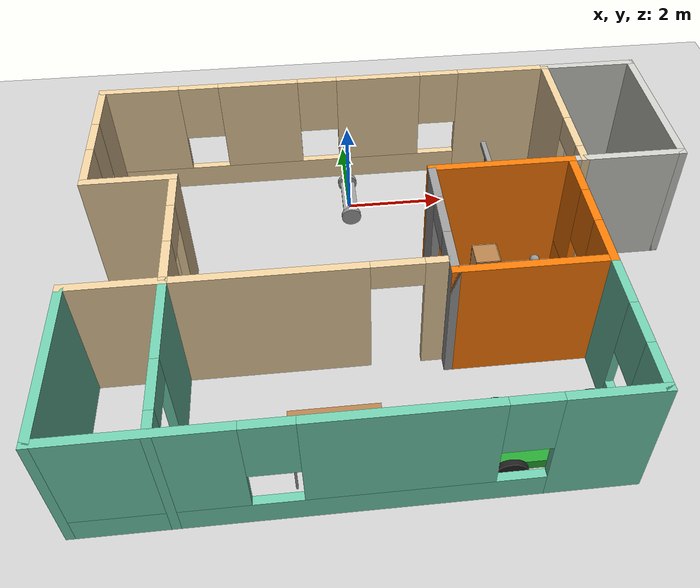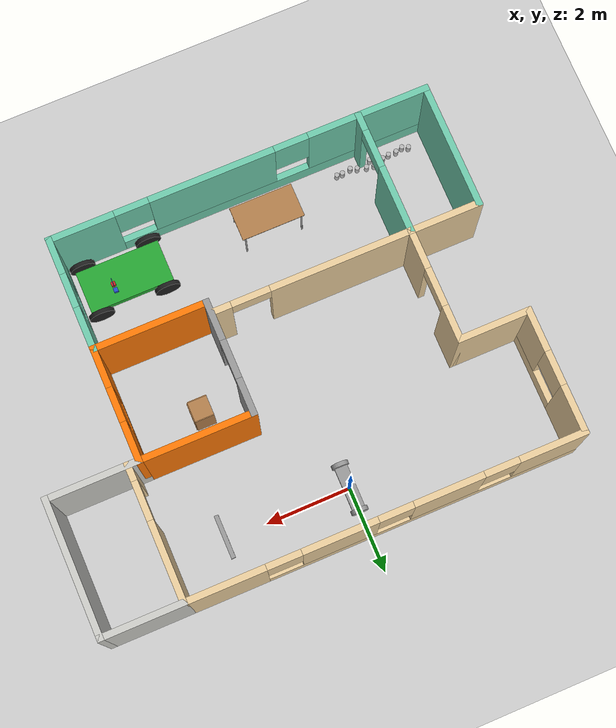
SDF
<sdf version="1.6">
 <world name="default">
  <plugin name="hello" filename="libhello.so"/>
  <plugin name="hello" filename="libhello.so"/>
  <plugin name="collision_map_creator" filename="libcollision_map_creator.so"/>
  <light name="sun" type="directional">
   <pose>0 0 10 0 -0 0</pose>
   <diffuse>0.8 0.8 0.8 1</diffuse>
   <specular>0.2 0.2 0.2 1</specular>
   <attenuation>
    <range>1000</range>
    <constant>0.9</constant>
    <linear>0.01</linear>
    <quadratic>0.001</quadratic>
   </attenuation>
   <direction>-0.5 0.1 -0.9</direction>
  </light>
  <model name="ground_plane">
   <static>1</static>
   <link name="link">
    <collision name="collision">
     <geometry><plane><normal>0 0 1</normal><size>100 100</size></plane></geometry>
     <surface>
      <contact><collide_bitmask>65535</collide_bitmask></contact>
      <friction><ode><mu>100</mu><mu2>50</mu2></ode></friction>
     </surface>
    </collision>
    <visual name="visual">
     <cast_shadows>0</cast_shadows>
     <geometry><plane><normal>0 0 1</normal><size>100 100</size></plane></geometry>
     <material>
      <script><uri>file://media/materials/scripts/gazebo.material</uri><name>Gazebo/Grey</name></script>
     </material>
    </visual>
   </link>
  </model>
  <gravity>0 0 -9.8</gravity>
  <magnetic_field>6e-06 2.3e-05 -4.2e-05</magnetic_field>
  <atmosphere type="adiabatic"/>
  <physics name="default_physics" default="0" type="ode">
   <max_step_size>0.001</max_step_size>
   <real_time_factor>1</real_time_factor>
   <real_time_update_rate>1000</real_time_update_rate>
  </physics>
  <scene><ambient>0.4 0.4 0.4 1</ambient><background>0.7 0.7 0.7 1</background><shadows>1</shadows></scene>
  <spherical_coordinates>
   <surface_model>EARTH_WGS84</surface_model>
   <latitude_deg>0</latitude_deg>
   <longitude_deg>0</longitude_deg>
   <elevation>0</elevation>
   <heading_deg>0</heading_deg>
  </spherical_coordinates>
  <model name="robot">
   <link name="link_0">
    <inertial>
     <mass>1.10599</mass>
     <inertia>
      <ixx>0.204905</ixx>
      <ixy>0</ixy>
      <ixz>0</ixz>
      <iyy>0.204905</iyy>
      <iyz>0</iyz>
      <izz>0.184332</izz>
     </inertia>
    </inertial>
    <visual name="visual">
     <geometry><box><size>0.3 1 0.1</size></box></geometry>
     <material>
      <lighting>1</lighting>
      <script><uri>file://media/materials/scripts/gazebo.material</uri><name>Gazebo/Grey</name></script>
      <shader type="pixel"><normal_map>__default__</normal_map></shader>
      <ambient>0.3 0.3 0.3 1</ambient>
      <diffuse>0.7 0.7 0.7 1</diffuse>
      <specular>0.01 0.01 0.01 1</specular>
      <emissive>0 0 0 1</emissive>
     </material>
    </visual>
    <collision name="collision">
     <geometry><box><size>0.3 1 0.1</size></box></geometry>
     <surface>
      <friction>
       <ode><mu>1</mu><mu2>1</mu2><fdir1>0 0 0</fdir1><slip1>0</slip1><slip2>0</slip2></ode>
       <torsional>
        <coefficient>1</coefficient>
        <patch_radius>0</patch_radius>
        <surface_radius>0</surface_radius>
        <use_patch_radius>1</use_patch_radius>
        <ode><slip>0</slip></ode>
       </torsional>
      </friction>
      <bounce><restitution_coefficient>0</restitution_coefficient><threshold>1e+06</threshold></bounce>
      <contact>
       <collide_without_contact>0</collide_without_contact>
       <collide_without_contact_bitmask>1</collide_without_contact_bitmask>
       <collide_bitmask>1</collide_bitmask>
       <ode>
        <soft_cfm>0</soft_cfm>
        <soft_erp>0.2</soft_erp>
        <kp>1e+13</kp>
        <kd>1</kd>
        <max_vel>0.01</max_vel>
        <min_depth>0</min_depth>
       </ode>
       <bullet>
        <split_impulse>1</split_impulse>
        <split_impulse_penetration_threshold>-0.01</split_impulse_penetration_threshold>
        <soft_cfm>0</soft_cfm>
        <soft_erp>0.2</soft_erp>
        <kp>1e+13</kp>
        <kd>1</kd>
       </bullet>
      </contact>
     </surface>
    </collision>
   </link>
   <link name="link_1">
    <pose>0 -0.550001 0 1.57079 -0 0</pose>
    <inertial>
     <mass>1</mass>
     <inertia><ixx>0.145833</ixx><ixy>0</ixy><ixz>0</ixz><iyy>0.145833</iyy><iyz>0</iyz><izz>0.125</izz></inertia>
    </inertial>
    <visual name="visual">
     <geometry><cylinder><radius>0.2</radius><length>0.1</length></cylinder></geometry>
     <material>
      <lighting>1</lighting>
      <script><uri>file://media/materials/scripts/gazebo.material</uri><name>Gazebo/Grey</name></script>
      <shader type="pixel"><normal_map>__default__</normal_map></shader>
      <ambient>0.3 0.3 0.3 1</ambient>
      <diffuse>0.7 0.7 0.7 1</diffuse>
      <specular>0.01 0.01 0.01 1</specular>
      <emissive>0 0 0 1</emissive>
     </material>
    </visual>
    <collision name="collision">
     <geometry><cylinder><radius>0.2</radius><length>0.1</length></cylinder></geometry>
     <surface>
      <friction>
       <ode><mu>1</mu><mu2>1</mu2><fdir1>0 0 0</fdir1><slip1>0</slip1><slip2>0</slip2></ode>
       <torsional>
        <coefficient>1</coefficient>
        <patch_radius>0</patch_radius>
        <surface_radius>0</surface_radius>
        <use_patch_radius>1</use_patch_radius>
        <ode><slip>0</slip></ode>
       </torsional>
      </friction>
      <bounce><restitution_coefficient>0</restitution_coefficient><threshold>1e+06</threshold></bounce>
      <contact>
       <collide_without_contact>0</collide_without_contact>
       <collide_without_contact_bitmask>1</collide_without_contact_bitmask>
       <collide_bitmask>1</collide_bitmask>
       <ode>
        <soft_cfm>0</soft_cfm>
        <soft_erp>0.2</soft_erp>
        <kp>1e+13</kp>
        <kd>1</kd>
        <max_vel>0.01</max_vel>
        <min_depth>0</min_depth>
       </ode>
       <bullet>
        <split_impulse>1</split_impulse>
        <split_impulse_penetration_threshold>-0.01</split_impulse_penetration_threshold>
        <soft_cfm>0</soft_cfm>
        <soft_erp>0.2</soft_erp>
        <kp>1e+13</kp>
        <kd>1</kd>
       </bullet>
      </contact>
     </surface>
    </collision>
   </link>
   <link name="link_1_clone">
    <pose>0 0.550001 0 1.57079 -0 0</pose>
    <inertial>
     <mass>1</mass>
     <inertia><ixx>0.145833</ixx><ixy>0</ixy><ixz>0</ixz><iyy>0.145833</iyy><iyz>0</iyz><izz>0.125</izz></inertia>
    </inertial>
    <visual name="visual">
     <geometry><cylinder><radius>0.2</radius><length>0.1</length></cylinder></geometry>
     <material>
      <lighting>1</lighting>
      <script><uri>file://media/materials/scripts/gazebo.material</uri><name>Gazebo/Grey</name></script>
      <shader type="pixel"><normal_map>__default__</normal_map></shader>
      <ambient>0.3 0.3 0.3 1</ambient>
      <diffuse>0.7 0.7 0.7 1</diffuse>
      <specular>0.01 0.01 0.01 1</specular>
      <emissive>0 0 0 1</emissive>
     </material>
    </visual>
    <collision name="collision">
     <geometry><cylinder><radius>0.2</radius><length>0.1</length></cylinder></geometry>
     <surface>
      <friction>
       <ode><mu>1</mu><mu2>1</mu2><fdir1>0 0 0</fdir1><slip1>0</slip1><slip2>0</slip2></ode>
       <torsional>
        <coefficient>1</coefficient>
        <patch_radius>0</patch_radius>
        <surface_radius>0</surface_radius>
        <use_patch_radius>1</use_patch_radius>
        <ode><slip>0</slip></ode>
       </torsional>
      </friction>
      <bounce><restitution_coefficient>0</restitution_coefficient><threshold>1e+06</threshold></bounce>
      <contact>
       <collide_without_contact>0</collide_without_contact>
       <collide_without_contact_bitmask>1</collide_without_contact_bitmask>
       <collide_bitmask>1</collide_bitmask>
       <ode>
        <soft_cfm>0</soft_cfm>
        <soft_erp>0.2</soft_erp>
        <kp>1e+13</kp>
        <kd>1</kd>
        <max_vel>0.01</max_vel>
        <min_depth>0</min_depth>
       </ode>
       <bullet>
        <split_impulse>1</split_impulse>
        <split_impulse_penetration_threshold>-0.01</split_impulse_penetration_threshold>
        <soft_cfm>0</soft_cfm>
        <soft_erp>0.2</soft_erp>
        <kp>1e+13</kp>
        <kd>1</kd>
       </bullet>
      </contact>
     </surface>
    </collision>
   </link>
   <joint name="link_0_JOINT_0" type="revolute">
    <parent>link_0</parent>
    <child>link_1</child>
    <axis>
     <xyz>0 0 1</xyz>
     <use_parent_model_frame>0</use_parent_model_frame>
     <limit>
      <lower>-1.79769e+308</lower>
      <upper>1.79769e+308</upper>
      <effort>-1</effort>
      <velocity>-1</velocity>
     </limit>
     <dynamics>
      <spring_reference>0</spring_reference>
      <spring_stiffness>0</spring_stiffness>
      <damping>0</damping>
     </dynamics>
    </axis>
    <physics>
     <ode><limit><cfm>0</cfm><erp>0.2</erp></limit><suspension><cfm>0</cfm><erp>0.2</erp></suspension></ode>
    </physics>
   </joint>
   <joint name="link_0_JOINT_1" type="revolute">
    <parent>link_0</parent>
    <child>link_1_clone</child>
    <axis>
     <xyz>0 0 1</xyz>
     <use_parent_model_frame>0</use_parent_model_frame>
     <limit>
      <lower>-1.79769e+308</lower>
      <upper>1.79769e+308</upper>
      <effort>-1</effort>
      <velocity>-1</velocity>
     </limit>
     <dynamics>
      <spring_reference>0</spring_reference>
      <spring_stiffness>0</spring_stiffness>
      <damping>0</damping>
     </dynamics>
    </axis>
    <physics>
     <ode><limit><cfm>0</cfm><erp>0.2</erp></limit><suspension><cfm>0</cfm><erp>0.2</erp></suspension></ode>
    </physics>
   </joint>
   <static>0</static>
   <pose>0 -1e-06 0.2 0 -0 0</pose>
  </model>
  <model name="anotherrone_clone_0">
   <link name="link_0_clone">
    <pose>1.00397 -1.20326 1.05 1.57079 -0 0</pose>
    <inertial>
     <mass>1</mass>
     <inertia>
      <ixx>0.166667</ixx>
      <ixy>0</ixy>
      <ixz>0</ixz>
      <iyy>0.166667</iyy>
      <iyz>0</iyz>
      <izz>0.166667</izz>
     </inertia>
    </inertial>
    <visual name="visual">
     <geometry><box><size>0.1 0.1 1</size></box></geometry>
     <material>
      <lighting>1</lighting>
      <script><uri>file://media/materials/scripts/gazebo.material</uri><name>Gazebo/Grey</name></script>
      <shader type="pixel"><normal_map>__default__</normal_map></shader>
      <ambient>0.3 0.3 0.3 1</ambient>
      <diffuse>0.7 0.7 0.7 1</diffuse>
      <specular>0.01 0.01 0.01 1</specular>
      <emissive>0 0 0 1</emissive>
     </material>
    </visual>
    <collision name="collision">
     <geometry><box><size>0.1 0.1 1</size></box></geometry>
     <surface>
      <friction>
       <ode><mu>1</mu><mu2>1</mu2><fdir1>0 0 0</fdir1><slip1>0</slip1><slip2>0</slip2></ode>
       <torsional>
        <coefficient>1</coefficient>
        <patch_radius>0</patch_radius>
        <surface_radius>0</surface_radius>
        <use_patch_radius>1</use_patch_radius>
        <ode><slip>0</slip></ode>
       </torsional>
      </friction>
      <bounce><restitution_coefficient>0</restitution_coefficient><threshold>1e+06</threshold></bounce>
      <contact>
       <collide_without_contact>0</collide_without_contact>
       <collide_without_contact_bitmask>1</collide_without_contact_bitmask>
       <collide_bitmask>1</collide_bitmask>
       <ode>
        <soft_cfm>0</soft_cfm>
        <soft_erp>0.2</soft_erp>
        <kp>1e+13</kp>
        <kd>1</kd>
        <max_vel>0.01</max_vel>
        <min_depth>0</min_depth>
       </ode>
       <bullet>
        <split_impulse>1</split_impulse>
        <split_impulse_penetration_threshold>-0.01</split_impulse_penetration_threshold>
        <soft_cfm>0</soft_cfm>
        <soft_erp>0.2</soft_erp>
        <kp>1e+13</kp>
        <kd>1</kd>
       </bullet>
      </contact>
     </surface>
    </collision>
   </link>
   <link name="link_0_clone_clone">
    <pose>1.00397 -1.20326 0.499999 0 -0 0</pose>
    <inertial>
     <mass>1</mass>
     <inertia>
      <ixx>0.166667</ixx>
      <ixy>0</ixy>
      <ixz>0</ixz>
      <iyy>0.166667</iyy>
      <iyz>0</iyz>
      <izz>0.166667</izz>
     </inertia>
    </inertial>
    <visual name="visual">
     <geometry><box><size>0.1 0.1 1</size></box></geometry>
     <material>
      <lighting>1</lighting>
      <script><uri>file://media/materials/scripts/gazebo.material</uri><name>Gazebo/Grey</name></script>
      <shader type="pixel"><normal_map>__default__</normal_map></shader>
      <ambient>0.3 0.3 0.3 1</ambient>
      <diffuse>0.7 0.7 0.7 1</diffuse>
      <specular>0.01 0.01 0.01 1</specular>
      <emissive>0 0 0 1</emissive>
     </material>
    </visual>
    <collision name="collision">
     <geometry><box><size>0.1 0.1 1</size></box></geometry>
     <surface>
      <friction>
       <ode><mu>1</mu><mu2>1</mu2><fdir1>0 0 0</fdir1><slip1>0</slip1><slip2>0</slip2></ode>
       <torsional>
        <coefficient>1</coefficient>
        <patch_radius>0</patch_radius>
        <surface_radius>0</surface_radius>
        <use_patch_radius>1</use_patch_radius>
        <ode><slip>0</slip></ode>
       </torsional>
      </friction>
      <bounce><restitution_coefficient>0</restitution_coefficient><threshold>1e+06</threshold></bounce>
      <contact>
       <collide_without_contact>0</collide_without_contact>
       <collide_without_contact_bitmask>1</collide_without_contact_bitmask>
       <collide_bitmask>1</collide_bitmask>
       <ode>
        <soft_cfm>0</soft_cfm>
        <soft_erp>0.2</soft_erp>
        <kp>1e+13</kp>
        <kd>1</kd>
        <max_vel>0.01</max_vel>
        <min_depth>0</min_depth>
       </ode>
       <bullet>
        <split_impulse>1</split_impulse>
        <split_impulse_penetration_threshold>-0.01</split_impulse_penetration_threshold>
        <soft_cfm>0</soft_cfm>
        <soft_erp>0.2</soft_erp>
        <kp>1e+13</kp>
        <kd>1</kd>
       </bullet>
      </contact>
     </surface>
    </collision>
   </link>
   <joint name="link_0_clone_clone_JOINT_0" type="revolute">
    <parent>link_0_clone_clone</parent>
    <child>link_0_clone</child>
    <axis>
     <xyz>0 -1 0</xyz>
     <use_parent_model_frame>0</use_parent_model_frame>
     <limit>
      <lower>-1.79769e+308</lower>
      <upper>1.79769e+308</upper>
      <effort>-1</effort>
      <velocity>-1</velocity>
     </limit>
     <dynamics>
      <spring_reference>0</spring_reference>
      <spring_stiffness>0</spring_stiffness>
      <damping>0</damping>
     </dynamics>
    </axis>
    <physics>
     <ode><limit><cfm>0</cfm><erp>0.2</erp></limit><suspension><cfm>0</cfm><erp>0.2</erp></suspension></ode>
    </physics>
   </joint>
   <static>0</static>
   <pose>1.95544 1.23394 1e-05 4e-06 4e-06 4.4e-05</pose>
  </model>
  <model name="my_ball">
   <link name="link">
    <inertial>
     <mass>1</mass>
     <inertia><ixx>0.1</ixx><ixy>0</ixy><ixz>0</ixz><iyy>0.1</iyy><iyz>0</iyz><izz>0.1</izz></inertia>
    </inertial>
    <visual name="visual">
     <geometry><sphere><radius>0.1</radius></sphere></geometry>
     <material>
      <script><name>Gazebo/Grey</name><uri>file://media/materials/scripts/gazebo.material</uri></script>
      <shader type="pixel"><normal_map>__default__</normal_map></shader>
      <ambient>1 1 1 1</ambient>
      <diffuse>1 1 1 1</diffuse>
      <specular>1 1 1 1</specular>
      <emissive>1 1 1 1</emissive>
     </material>
    </visual>
    <collision name="collision">
     <geometry><sphere><radius>0.1</radius></sphere></geometry>
     <surface>
      <friction>
       <ode><mu>1</mu><mu2>1</mu2><fdir1>0 0 0</fdir1><slip1>0</slip1><slip2>0</slip2></ode>
       <torsional>
        <coefficient>1</coefficient>
        <patch_radius>0</patch_radius>
        <surface_radius>0</surface_radius>
        <use_patch_radius>1</use_patch_radius>
        <ode><slip>0</slip></ode>
       </torsional>
      </friction>
      <bounce><restitution_coefficient>0</restitution_coefficient><threshold>1e+06</threshold></bounce>
      <contact>
       <collide_without_contact>0</collide_without_contact>
       <collide_without_contact_bitmask>1</collide_without_contact_bitmask>
       <collide_bitmask>1</collide_bitmask>
       <ode>
        <soft_cfm>0</soft_cfm>
        <soft_erp>0.2</soft_erp>
        <kp>1e+13</kp>
        <kd>1</kd>
        <max_vel>0.01</max_vel>
        <min_depth>0</min_depth>
       </ode>
       <bullet>
        <split_impulse>1</split_impulse>
        <split_impulse_penetration_threshold>-0.01</split_impulse_penetration_threshold>
        <soft_cfm>0</soft_cfm>
        <soft_erp>0.2</soft_erp>
        <kp>1e+13</kp>
        <kd>1</kd>
       </bullet>
      </contact>
     </surface>
    </collision>
   </link>
   <static>0</static>
   <pose>3.57794 -2.15315 0.1 0.017034 -0 0</pose>
  </model>
  <model name="cabinet">
   <static>1</static>
   <link name="cabinet_bottom_plate">
    <inertial>
     <pose>0 0 -1 0 -0 0</pose>
     <inertia><ixx>2.05</ixx><ixy>0</ixy><ixz>0</ixz><iyy>2.05</iyy><iyz>0</iyz><izz>2.05</izz></inertia>
     <mass>25</mass>
    </inertial>
    <collision name="cabinet_bottom_plate_geom">
     <pose>0 0 0.01 0 -0 0</pose>
     <geometry><box><size>0.45 0.45 0.02</size></box></geometry>
    </collision>
    <visual name="cabinet_bottom_plate_geom_visual">
     <pose>0 0 0.01 0 -0 0</pose>
     <geometry><box><size>0.45 0.45 0.02</size></box></geometry>
     <material>
      <script><uri>file://media/materials/scripts/gazebo.material</uri><name>Gazebo/Wood</name></script>
     </material>
    </visual>
    <collision name="cabinet_bottom_plate_geom_cabinet_back_plate">
     <pose>0.235 0 0.51 0 -0 0</pose>
     <geometry><box><size>0.02 0.45 1.02</size></box></geometry>
    </collision>
    <visual name="cabinet_bottom_plate_geom_cabinet_back_plate_visual">
     <pose>0.235 0 0.51 0 -0 0</pose>
     <geometry><box><size>0.02 0.45 1.02</size></box></geometry>
     <material>
      <script><uri>file://media/materials/scripts/gazebo.material</uri><name>Gazebo/Wood</name></script>
     </material>
    </visual>
    <collision name="cabinet_bottom_plate_geom_cabinet_left_plate">
     <pose>0 0.235 0.51 0 -0 0</pose>
     <geometry><box><size>0.45 0.02 1.02</size></box></geometry>
    </collision>
    <visual name="cabinet_bottom_plate_geom_cabinet_left_plate_visual">
     <pose>0 0.235 0.51 0 -0 0</pose>
     <geometry><box><size>0.45 0.02 1.02</size></box></geometry>
     <material>
      <script><uri>file://media/materials/scripts/gazebo.material</uri><name>Gazebo/Wood</name></script>
     </material>
    </visual>
    <collision name="cabinet_bottom_plate_geom_cabinet_middle_plate">
     <pose>0 0 0.51 0 -0 0</pose>
     <geometry><box><size>0.45 0.45 0.02</size></box></geometry>
    </collision>
    <visual name="cabinet_bottom_plate_geom_cabinet_middle_plate_visual">
     <pose>0 0 0.51 0 -0 0</pose>
     <geometry><box><size>0.45 0.45 0.02</size></box></geometry>
     <material>
      <script><uri>file://media/materials/scripts/gazebo.material</uri><name>Gazebo/Wood</name></script>
     </material>
    </visual>
    <collision name="cabinet_bottom_plate_geom_cabinet_right_plate">
     <pose>0 -0.235 0.51 0 -0 0</pose>
     <geometry><box><size>0.45 0.02 1.02</size></box></geometry>
    </collision>
    <visual name="cabinet_bottom_plate_geom_cabinet_right_plate_visual">
     <pose>0 -0.235 0.51 0 -0 0</pose>
     <geometry><box><size>0.45 0.02 1.02</size></box></geometry>
     <material>
      <script><uri>file://media/materials/scripts/gazebo.material</uri><name>Gazebo/Wood</name></script>
     </material>
    </visual>
    <collision name="cabinet_bottom_plate_geom_cabinet_top_plate">
     <pose>0 0 1.01 0 -0 0</pose>
     <geometry><box><size>0.45 0.45 0.02</size></box></geometry>
    </collision>
    <visual name="cabinet_bottom_plate_geom_cabinet_top_plate_visual">
     <pose>0 0 1.01 0 -0 0</pose>
     <geometry><box><size>0.45 0.45 0.02</size></box></geometry>
     <material>
      <script><uri>file://media/materials/scripts/gazebo.material</uri><name>Gazebo/Wood</name></script>
     </material>
    </visual>
   </link>
   <pose>2.37507 -2.78574 0 0 -0 0</pose>
  </model>
  <model name="beer">
   <link name="link">
    <pose>0 0 0.115 0 -0 0</pose>
    <inertial>
     <mass>0.39</mass>
     <inertia><ixx>0.00058</ixx><ixy>0</ixy><ixz>0</ixz><iyy>0.00058</iyy><iyz>0</iyz><izz>0.00019</izz></inertia>
    </inertial>
    <collision name="collision">
     <geometry><cylinder><radius>0.055</radius><length>0.23</length></cylinder></geometry>
    </collision>
    <visual name="visual">
     <geometry><cylinder><radius>0.055</radius><length>0.23</length></cylinder></geometry>
     <material>
      <script>
       <uri>model://beer/materials/scripts</uri>
       <uri>model://beer/materials/textures</uri>
       <name>Beer/Diffuse</name>
      </script>
     </material>
    </visual>
   </link>
   <pose>-2.60192 -6.78865 -8e-06 -1e-06 -0 -2.8e-05</pose>
  </model>
  <model name="beer_0">
   <link name="link">
    <pose>0 0 0.115 0 -0 0</pose>
    <inertial>
     <mass>0.39</mass>
     <inertia><ixx>0.00058</ixx><ixy>0</ixy><ixz>0</ixz><iyy>0.00058</iyy><iyz>0</iyz><izz>0.00019</izz></inertia>
    </inertial>
    <collision name="collision">
     <geometry><cylinder><radius>0.055</radius><length>0.23</length></cylinder></geometry>
    </collision>
    <visual name="visual">
     <geometry><cylinder><radius>0.055</radius><length>0.23</length></cylinder></geometry>
     <material>
      <script>
       <uri>model://beer/materials/scripts</uri>
       <uri>model://beer/materials/textures</uri>
       <name>Beer/Diffuse</name>
      </script>
     </material>
    </visual>
   </link>
   <pose>-2.73761 -6.78616 -8e-06 -1e-06 -0 -2.4e-05</pose>
  </model>
  <model name="beer_1">
   <link name="link">
    <pose>0 0 0.115 0 -0 0</pose>
    <inertial>
     <mass>0.39</mass>
     <inertia><ixx>0.00058</ixx><ixy>0</ixy><ixz>0</ixz><iyy>0.00058</iyy><iyz>0</iyz><izz>0.00019</izz></inertia>
    </inertial>
    <collision name="collision">
     <geometry><cylinder><radius>0.055</radius><length>0.23</length></cylinder></geometry>
    </collision>
    <visual name="visual">
     <geometry><cylinder><radius>0.055</radius><length>0.23</length></cylinder></geometry>
     <material>
      <script>
       <uri>model://beer/materials/scripts</uri>
       <uri>model://beer/materials/textures</uri>
       <name>Beer/Diffuse</name>
      </script>
     </material>
    </visual>
   </link>
   <pose>-2.94651 -6.81855 -2e-06 0 0 -2.3e-05</pose>
  </model>
  <model name="beer_2">
   <link name="link">
    <pose>0 0 0.115 0 -0 0</pose>
    <inertial>
     <mass>0.39</mass>
     <inertia><ixx>0.00058</ixx><ixy>0</ixy><ixz>0</ixz><iyy>0.00058</iyy><iyz>0</iyz><izz>0.00019</izz></inertia>
    </inertial>
    <collision name="collision">
     <geometry><cylinder><radius>0.055</radius><length>0.23</length></cylinder></geometry>
    </collision>
    <visual name="visual">
     <geometry><cylinder><radius>0.055</radius><length>0.23</length></cylinder></geometry>
     <material>
      <script>
       <uri>model://beer/materials/scripts</uri>
       <uri>model://beer/materials/textures</uri>
       <name>Beer/Diffuse</name>
      </script>
     </material>
    </visual>
   </link>
   <pose>-3.10064 -6.75988 -8e-06 -1e-06 -0 -2.3e-05</pose>
  </model>
  <model name="beer_3">
   <link name="link">
    <pose>0 0 0.115 0 -0 0</pose>
    <inertial>
     <mass>0.39</mass>
     <inertia><ixx>0.00058</ixx><ixy>0</ixy><ixz>0</ixz><iyy>0.00058</iyy><iyz>0</iyz><izz>0.00019</izz></inertia>
    </inertial>
    <collision name="collision">
     <geometry><cylinder><radius>0.055</radius><length>0.23</length></cylinder></geometry>
    </collision>
    <visual name="visual">
     <geometry><cylinder><radius>0.055</radius><length>0.23</length></cylinder></geometry>
     <material>
      <script>
       <uri>model://beer/materials/scripts</uri>
       <uri>model://beer/materials/textures</uri>
       <name>Beer/Diffuse</name>
      </script>
     </material>
    </visual>
   </link>
   <pose>-3.31312 -6.70602 -2e-06 0 -0 1.4e-05</pose>
  </model>
  <model name="beer_4">
   <link name="link">
    <pose>0 0 0.115 0 -0 0</pose>
    <inertial>
     <mass>0.39</mass>
     <inertia><ixx>0.00058</ixx><ixy>0</ixy><ixz>0</ixz><iyy>0.00058</iyy><iyz>0</iyz><izz>0.00019</izz></inertia>
    </inertial>
    <collision name="collision">
     <geometry><cylinder><radius>0.055</radius><length>0.23</length></cylinder></geometry>
    </collision>
    <visual name="visual">
     <geometry><cylinder><radius>0.055</radius><length>0.23</length></cylinder></geometry>
     <material>
      <script>
       <uri>model://beer/materials/scripts</uri>
       <uri>model://beer/materials/textures</uri>
       <name>Beer/Diffuse</name>
      </script>
     </material>
    </visual>
   </link>
   <pose>-3.49304 -6.67884 -8e-06 -1e-06 -0 -2e-05</pose>
  </model>
  <model name="beer_5">
   <link name="link">
    <pose>0 0 0.115 0 -0 0</pose>
    <inertial>
     <mass>0.39</mass>
     <inertia><ixx>0.00058</ixx><ixy>0</ixy><ixz>0</ixz><iyy>0.00058</iyy><iyz>0</iyz><izz>0.00019</izz></inertia>
    </inertial>
    <collision name="collision">
     <geometry><cylinder><radius>0.055</radius><length>0.23</length></cylinder></geometry>
    </collision>
    <visual name="visual">
     <geometry><cylinder><radius>0.055</radius><length>0.23</length></cylinder></geometry>
     <material>
      <script>
       <uri>model://beer/materials/scripts</uri>
       <uri>model://beer/materials/textures</uri>
       <name>Beer/Diffuse</name>
      </script>
     </material>
    </visual>
   </link>
   <pose>-3.4471 -6.83729 -2e-06 0 0 -1.9e-05</pose>
  </model>
  <model name="beer_6">
   <link name="link">
    <pose>0 0 0.115 0 -0 0</pose>
    <inertial>
     <mass>0.39</mass>
     <inertia><ixx>0.00058</ixx><ixy>0</ixy><ixz>0</ixz><iyy>0.00058</iyy><iyz>0</iyz><izz>0.00019</izz></inertia>
    </inertial>
    <collision name="collision">
     <geometry><cylinder><radius>0.055</radius><length>0.23</length></cylinder></geometry>
    </collision>
    <visual name="visual">
     <geometry><cylinder><radius>0.055</radius><length>0.23</length></cylinder></geometry>
     <material>
      <script>
       <uri>model://beer/materials/scripts</uri>
       <uri>model://beer/materials/textures</uri>
       <name>Beer/Diffuse</name>
      </script>
     </material>
    </visual>
   </link>
   <pose>-3.61904 -6.82708 -8e-06 -1e-06 -0 -2e-05</pose>
  </model>
  <model name="beer_7">
   <link name="link">
    <pose>0 0 0.115 0 -0 0</pose>
    <inertial>
     <mass>0.39</mass>
     <inertia><ixx>0.00058</ixx><ixy>0</ixy><ixz>0</ixz><iyy>0.00058</iyy><iyz>0</iyz><izz>0.00019</izz></inertia>
    </inertial>
    <collision name="collision">
     <geometry><cylinder><radius>0.055</radius><length>0.23</length></cylinder></geometry>
    </collision>
    <visual name="visual">
     <geometry><cylinder><radius>0.055</radius><length>0.23</length></cylinder></geometry>
     <material>
      <script>
       <uri>model://beer/materials/scripts</uri>
       <uri>model://beer/materials/textures</uri>
       <name>Beer/Diffuse</name>
      </script>
     </material>
    </visual>
   </link>
   <pose>-3.73869 -6.75497 -2e-06 0 0 -1.8e-05</pose>
  </model>
  <model name="beer_8">
   <link name="link">
    <pose>0 0 0.115 0 -0 0</pose>
    <inertial>
     <mass>0.39</mass>
     <inertia><ixx>0.00058</ixx><ixy>0</ixy><ixz>0</ixz><iyy>0.00058</iyy><iyz>0</iyz><izz>0.00019</izz></inertia>
    </inertial>
    <collision name="collision">
     <geometry><cylinder><radius>0.055</radius><length>0.23</length></cylinder></geometry>
    </collision>
    <visual name="visual">
     <geometry><cylinder><radius>0.055</radius><length>0.23</length></cylinder></geometry>
     <material>
      <script>
       <uri>model://beer/materials/scripts</uri>
       <uri>model://beer/materials/textures</uri>
       <name>Beer/Diffuse</name>
      </script>
     </material>
    </visual>
   </link>
   <pose>-3.89641 -6.78632 -8e-06 -1e-06 -0 -1.7e-05</pose>
  </model>
  <model name="beer_9">
   <link name="link">
    <pose>0 0 0.115 0 -0 0</pose>
    <inertial>
     <mass>0.39</mass>
     <inertia><ixx>0.00058</ixx><ixy>0</ixy><ixz>0</ixz><iyy>0.00058</iyy><iyz>0</iyz><izz>0.00019</izz></inertia>
    </inertial>
    <collision name="collision">
     <geometry><cylinder><radius>0.055</radius><length>0.23</length></cylinder></geometry>
    </collision>
    <visual name="visual">
     <geometry><cylinder><radius>0.055</radius><length>0.23</length></cylinder></geometry>
     <material>
      <script>
       <uri>model://beer/materials/scripts</uri>
       <uri>model://beer/materials/textures</uri>
       <name>Beer/Diffuse</name>
      </script>
     </material>
    </visual>
   </link>
   <pose>-4.08773 -6.78622 -2e-06 0 0 -1.6e-05</pose>
  </model>
  <model name="beer_10">
   <link name="link">
    <pose>0 0 0.115 0 -0 0</pose>
    <inertial>
     <mass>0.39</mass>
     <inertia><ixx>0.00058</ixx><ixy>0</ixy><ixz>0</ixz><iyy>0.00058</iyy><iyz>0</iyz><izz>0.00019</izz></inertia>
    </inertial>
    <collision name="collision">
     <geometry><cylinder><radius>0.055</radius><length>0.23</length></cylinder></geometry>
    </collision>
    <visual name="visual">
     <geometry><cylinder><radius>0.055</radius><length>0.23</length></cylinder></geometry>
     <material>
      <script>
       <uri>model://beer/materials/scripts</uri>
       <uri>model://beer/materials/textures</uri>
       <name>Beer/Diffuse</name>
      </script>
     </material>
    </visual>
   </link>
   <pose>-4.25212 -6.82846 -8e-06 -1e-06 -0 -1.6e-05</pose>
  </model>
  <model name="beer_11">
   <link name="link">
    <pose>0 0 0.115 0 -0 0</pose>
    <inertial>
     <mass>0.39</mass>
     <inertia><ixx>0.00058</ixx><ixy>0</ixy><ixz>0</ixz><iyy>0.00058</iyy><iyz>0</iyz><izz>0.00019</izz></inertia>
    </inertial>
    <collision name="collision">
     <geometry><cylinder><radius>0.055</radius><length>0.23</length></cylinder></geometry>
    </collision>
    <visual name="visual">
     <geometry><cylinder><radius>0.055</radius><length>0.23</length></cylinder></geometry>
     <material>
      <script>
       <uri>model://beer/materials/scripts</uri>
       <uri>model://beer/materials/textures</uri>
       <name>Beer/Diffuse</name>
      </script>
     </material>
    </visual>
   </link>
   <pose>-4.39553 -6.77114 -2e-06 0 0 -1.4e-05</pose>
  </model>
  <model name="car">
   <link name="chassis">
    <pose>0 0 0.3 0 -0 0</pose>
    <collision name="collision"><geometry><box><size>2 1 0.2</size></box></geometry></collision>
    <visual name="visual">
     <geometry><box><size>2 1 0.2</size></box></geometry>
     <material>
      <script><uri>file://media/materials/scripts/gazebo.material</uri><name>Gazebo/Green</name></script>
     </material>
    </visual>
    <inertial>
     <inertia><ixx>1</ixx><ixy>0</ixy><ixz>0</ixz><iyy>1</iyy><iyz>0</iyz><izz>1</izz></inertia>
     <mass>1</mass>
    </inertial>
   </link>
   <link name="front_left_wheel">
    <pose>0.8 0.6 0.3 -0 1.5707 1.5707</pose>
    <collision name="collision">
     <geometry><cylinder><radius>0.3</radius><length>0.1</length></cylinder></geometry>
    </collision>
    <visual name="visual">
     <geometry><cylinder><radius>0.3</radius><length>0.1</length></cylinder></geometry>
     <material>
      <script><uri>file://media/materials/scripts/gazebo.material</uri><name>Gazebo/Black</name></script>
     </material>
    </visual>
    <inertial>
     <inertia><ixx>1</ixx><ixy>0</ixy><ixz>0</ixz><iyy>1</iyy><iyz>0</iyz><izz>1</izz></inertia>
     <mass>1</mass>
    </inertial>
   </link>
   <link name="front_right_wheel">
    <pose>0.8 -0.6 0.3 -0 1.5707 1.5707</pose>
    <collision name="collision">
     <geometry><cylinder><radius>0.3</radius><length>0.1</length></cylinder></geometry>
    </collision>
    <visual name="visual">
     <geometry><cylinder><radius>0.3</radius><length>0.1</length></cylinder></geometry>
     <material>
      <script><uri>file://media/materials/scripts/gazebo.material</uri><name>Gazebo/Black</name></script>
     </material>
    </visual>
    <inertial>
     <inertia><ixx>1</ixx><ixy>0</ixy><ixz>0</ixz><iyy>1</iyy><iyz>0</iyz><izz>1</izz></inertia>
     <mass>1</mass>
    </inertial>
   </link>
   <link name="back_right_wheel">
    <pose>-0.8 -0.6 0.3 -0 1.5707 1.5707</pose>
    <collision name="collision">
     <geometry><cylinder><radius>0.3</radius><length>0.1</length></cylinder></geometry>
    </collision>
    <visual name="visual">
     <geometry><cylinder><radius>0.3</radius><length>0.1</length></cylinder></geometry>
     <material>
      <script><uri>file://media/materials/scripts/gazebo.material</uri><name>Gazebo/Black</name></script>
     </material>
    </visual>
    <inertial>
     <inertia><ixx>1</ixx><ixy>0</ixy><ixz>0</ixz><iyy>1</iyy><iyz>0</iyz><izz>1</izz></inertia>
     <mass>1</mass>
    </inertial>
   </link>
   <link name="back_left_wheel">
    <pose>-0.8 0.6 0.3 -0 1.5707 1.5707</pose>
    <collision name="collision">
     <geometry><cylinder><radius>0.3</radius><length>0.1</length></cylinder></geometry>
    </collision>
    <visual name="visual">
     <geometry><cylinder><radius>0.3</radius><length>0.1</length></cylinder></geometry>
     <material>
      <script><uri>file://media/materials/scripts/gazebo.material</uri><name>Gazebo/Black</name></script>
     </material>
    </visual>
    <inertial>
     <inertia><ixx>1</ixx><ixy>0</ixy><ixz>0</ixz><iyy>1</iyy><iyz>0</iyz><izz>1</izz></inertia>
     <mass>1</mass>
    </inertial>
   </link>
   <link name="gas_pedal">
    <pose>0.3 0.1 0.5 0 -0 0</pose>
    <collision name="collision"><geometry><box><size>0.1 0.1 0.1</size></box></geometry></collision>
    <visual name="visual">
     <geometry><box><size>0.1 0.1 0.1</size></box></geometry>
     <material>
      <script><uri>file://media/materials/scripts/gazebo.material</uri><name>Gazebo/Red</name></script>
     </material>
    </visual>
    <inertial>
     <inertia><ixx>1</ixx><ixy>0</ixy><ixz>0</ixz><iyy>1</iyy><iyz>0</iyz><izz>1</izz></inertia>
     <mass>1</mass>
    </inertial>
   </link>
   <link name="brake_pedal">
    <pose>0.3 0.25 0.5 0 -0 0</pose>
    <collision name="collision"><geometry><box><size>0.1 0.1 0.1</size></box></geometry></collision>
    <visual name="visual">
     <geometry><box><size>0.1 0.1 0.1</size></box></geometry>
     <material>
      <script><uri>file://media/materials/scripts/gazebo.material</uri><name>Gazebo/Blue</name></script>
     </material>
    </visual>
    <inertial>
     <inertia><ixx>1</ixx><ixy>0</ixy><ixz>0</ixz><iyy>1</iyy><iyz>0</iyz><izz>1</izz></inertia>
     <mass>1</mass>
    </inertial>
   </link>
   <link name="steering_wheel">
    <pose>0.3 0.2 1 0 1.5707 0</pose>
    <collision name="collision">
     <geometry><cylinder><radius>0.1</radius><length>0.01</length></cylinder></geometry>
    </collision>
    <visual name="visual">
     <geometry><cylinder><radius>0.1</radius><length>0.01</length></cylinder></geometry>
     <material>
      <script><uri>file://media/materials/scripts/gazebo.material</uri><name>Gazebo/Blue</name></script>
     </material>
    </visual>
    <inertial>
     <inertia><ixx>1</ixx><ixy>0</ixy><ixz>0</ixz><iyy>1</iyy><iyz>0</iyz><izz>1</izz></inertia>
     <mass>1</mass>
    </inertial>
   </link>
   <joint name="gas_joint" type="prismatic">
    <parent>chassis</parent>
    <child>gas_pedal</child>
    <axis>
     <xyz>1 0 0</xyz>
     <limit><lower>0</lower><upper>0.2</upper></limit>
     <use_parent_model_frame>1</use_parent_model_frame>
     <dynamics><spring_reference>0</spring_reference><spring_stiffness>0</spring_stiffness></dynamics>
    </axis>
   </joint>
   <joint name="brake_joint" type="prismatic">
    <parent>chassis</parent>
    <child>brake_pedal</child>
    <axis>
     <xyz>1 0 0</xyz>
     <limit><lower>0</lower><upper>0.2</upper></limit>
     <use_parent_model_frame>1</use_parent_model_frame>
     <dynamics><spring_reference>0</spring_reference><spring_stiffness>0</spring_stiffness></dynamics>
    </axis>
   </joint>
   <joint name="steering_joint" type="revolute">
    <parent>chassis</parent>
    <child>steering_wheel</child>
    <axis>
     <xyz>1 0 0</xyz>
     <limit><lower>-7.853</lower><upper>7.853</upper></limit>
     <use_parent_model_frame>1</use_parent_model_frame>
     <dynamics><spring_reference>0</spring_reference><spring_stiffness>0</spring_stiffness></dynamics>
    </axis>
   </joint>
   <joint name="front_left_joint" type="revolute2">
    <parent>chassis</parent>
    <child>front_left_wheel</child>
    <axis>
     <xyz>0 0 1</xyz>
     <limit><lower>8.63568e-06</lower><upper>8.63568e-06</upper></limit>
     <use_parent_model_frame>1</use_parent_model_frame>
     <dynamics><spring_reference>0</spring_reference><spring_stiffness>0</spring_stiffness></dynamics>
    </axis>
    <axis2>
     <xyz>0 1 0</xyz>
     <use_parent_model_frame>1</use_parent_model_frame>
     <dynamics><spring_reference>0</spring_reference><spring_stiffness>0</spring_stiffness></dynamics>
    </axis2>
    <physics><ode><limit><cfm>0</cfm><erp>0.9</erp></limit></ode></physics>
   </joint>
   <joint name="front_right_joint" type="revolute2">
    <parent>chassis</parent>
    <child>front_right_wheel</child>
    <axis>
     <xyz>0 0 1</xyz>
     <limit><lower>8.63568e-06</lower><upper>8.63568e-06</upper></limit>
     <use_parent_model_frame>1</use_parent_model_frame>
     <dynamics><spring_reference>0</spring_reference><spring_stiffness>0</spring_stiffness></dynamics>
    </axis>
    <axis2>
     <xyz>0 1 0</xyz>
     <use_parent_model_frame>1</use_parent_model_frame>
     <dynamics><spring_reference>0</spring_reference><spring_stiffness>0</spring_stiffness></dynamics>
    </axis2>
    <physics><ode><limit><cfm>0</cfm><erp>0.9</erp></limit></ode></physics>
   </joint>
   <joint name="back_right_joint" type="revolute2">
    <parent>chassis</parent>
    <child>back_right_wheel</child>
    <axis>
     <xyz>0 0 1</xyz>
     <limit><lower>0</lower><upper>0</upper></limit>
     <use_parent_model_frame>1</use_parent_model_frame>
     <dynamics><spring_reference>0</spring_reference><spring_stiffness>0</spring_stiffness></dynamics>
    </axis>
    <axis2>
     <xyz>0 1 0</xyz>
     <use_parent_model_frame>1</use_parent_model_frame>
     <dynamics><spring_reference>0</spring_reference><spring_stiffness>0</spring_stiffness></dynamics>
    </axis2>
    <physics><ode><limit><cfm>0</cfm><erp>0.9</erp></limit></ode></physics>
   </joint>
   <joint name="back_left_joint" type="revolute2">
    <parent>chassis</parent>
    <child>back_left_wheel</child>
    <axis>
     <xyz>0 0 1</xyz>
     <limit><lower>0</lower><upper>0</upper></limit>
     <use_parent_model_frame>1</use_parent_model_frame>
     <dynamics><spring_reference>0</spring_reference><spring_stiffness>0</spring_stiffness></dynamics>
    </axis>
    <axis2>
     <xyz>0 1 0</xyz>
     <use_parent_model_frame>1</use_parent_model_frame>
     <dynamics><spring_reference>0</spring_reference><spring_stiffness>0</spring_stiffness></dynamics>
    </axis2>
    <physics><ode><limit><cfm>0</cfm><erp>0.9</erp></limit></ode></physics>
   </joint>
   <plugin name="vehicle" filename="libVehiclePlugin.so">
    <front_left>front_left_joint</front_left>
    <front_right>front_right_joint</front_right>
    <back_left>back_left_joint</back_left>
    <back_right>back_right_joint</back_right>
    <gas>gas_joint</gas>
    <brake>brake_joint</brake>
    <steering>steering_joint</steering>
    <front_power>10</front_power>
    <rear_power>10</rear_power>
    <tire_angle_range>0.5</tire_angle_range>
    <max_speed>10</max_speed>
    <aero_load>0.1</aero_load>
   </plugin>
   <pose>2.79488 -6.40236 -0.003308 -0.000272 0.00092 0.000531</pose>
  </model>
  <model name="table">
   <static>1</static>
   <link name="link">
    <collision name="surface">
     <pose>0 0 1 0 -0 0</pose>
     <geometry><box><size>1.5 0.8 0.03</size></box></geometry>
     <surface><friction><ode><mu>0.6</mu><mu2>0.6</mu2></ode></friction></surface>
    </collision>
    <visual name="visual1">
     <pose>0 0 1 0 -0 0</pose>
     <geometry><box><size>1.5 0.8 0.03</size></box></geometry>
     <material>
      <script><uri>file://media/materials/scripts/gazebo.material</uri><name>Gazebo/Wood</name></script>
     </material>
    </visual>
    <collision name="front_left_leg">
     <pose>0.68 0.38 0.5 0 -0 0</pose>
     <geometry><cylinder><radius>0.02</radius><length>1</length></cylinder></geometry>
    </collision>
    <visual name="front_left_leg">
     <pose>0.68 0.38 0.5 0 -0 0</pose>
     <geometry><cylinder><radius>0.02</radius><length>1</length></cylinder></geometry>
     <material>
      <script><uri>file://media/materials/scripts/gazebo.material</uri><name>Gazebo/Grey</name></script>
     </material>
    </visual>
    <collision name="front_right_leg">
     <pose>0.68 -0.38 0.5 0 -0 0</pose>
     <geometry><cylinder><radius>0.02</radius><length>1</length></cylinder></geometry>
    </collision>
    <visual name="front_right_leg">
     <pose>0.68 -0.38 0.5 0 -0 0</pose>
     <geometry><cylinder><radius>0.02</radius><length>1</length></cylinder></geometry>
     <material>
      <script><uri>file://media/materials/scripts/gazebo.material</uri><name>Gazebo/Grey</name></script>
     </material>
    </visual>
    <collision name="back_right_leg">
     <pose>-0.68 -0.38 0.5 0 -0 0</pose>
     <geometry><cylinder><radius>0.02</radius><length>1</length></cylinder></geometry>
    </collision>
    <visual name="back_right_leg">
     <pose>-0.68 -0.38 0.5 0 -0 0</pose>
     <geometry><cylinder><radius>0.02</radius><length>1</length></cylinder></geometry>
     <material>
      <script><uri>file://media/materials/scripts/gazebo.material</uri><name>Gazebo/Grey</name></script>
     </material>
    </visual>
    <collision name="back_left_leg">
     <pose>-0.68 0.38 0.5 0 -0 0</pose>
     <geometry><cylinder><radius>0.02</radius><length>1</length></cylinder></geometry>
    </collision>
    <visual name="back_left_leg">
     <pose>-0.68 0.38 0.5 0 -0 0</pose>
     <geometry><cylinder><radius>0.02</radius><length>1</length></cylinder></geometry>
     <material>
      <script><uri>file://media/materials/scripts/gazebo.material</uri><name>Gazebo/Grey</name></script>
     </material>
    </visual>
   </link>
   <pose>-0.699943 -6.36243 0 0 -0 0</pose>
  </model>
  <model name="someHouse">
   <link name="Wall_24">
    <pose>3.375 -1.55 0 0 -0 0</pose>
    <visual name="Wall_24_Visual">
     <pose>0 0 1.25 0 -0 0</pose>
     <geometry><box><size>2.75 0.15 2.5</size></box></geometry>
     <material>
      <script><uri>file://media/materials/scripts/gazebo.material</uri><name>Gazebo/Grey</name></script>
      <ambient>0.996078 0.47451 0.0196078 1</ambient>
      <shader type="pixel"/>
      <diffuse>0.7 0.7 0.7 1</diffuse>
      <specular>0.01 0.01 0.01 1</specular>
      <emissive>0 0 0 1</emissive>
     </material>
     <meta><layer>0</layer></meta>
    </visual>
    <collision name="Wall_24_Collision">
     <pose>0 0 1.25 0 -0 0</pose>
     <geometry><box><size>2.75 0.15 2.5</size></box></geometry>
     <surface>
      <friction>
       <ode><mu>1</mu><mu2>1</mu2><fdir1>0 0 0</fdir1><slip1>0</slip1><slip2>0</slip2></ode>
       <torsional>
        <coefficient>1</coefficient>
        <patch_radius>0</patch_radius>
        <surface_radius>0</surface_radius>
        <use_patch_radius>1</use_patch_radius>
        <ode><slip>0</slip></ode>
       </torsional>
      </friction>
      <bounce><restitution_coefficient>0</restitution_coefficient><threshold>1e+06</threshold></bounce>
      <contact>
       <collide_without_contact>0</collide_without_contact>
       <collide_without_contact_bitmask>1</collide_without_contact_bitmask>
       <collide_bitmask>1</collide_bitmask>
       <ode>
        <soft_cfm>0</soft_cfm>
        <soft_erp>0.2</soft_erp>
        <kp>1e+13</kp>
        <kd>1</kd>
        <max_vel>0.01</max_vel>
        <min_depth>0</min_depth>
       </ode>
       <bullet>
        <split_impulse>1</split_impulse>
        <split_impulse_penetration_threshold>-0.01</split_impulse_penetration_threshold>
        <soft_cfm>0</soft_cfm>
        <soft_erp>0.2</soft_erp>
        <kp>1e+13</kp>
        <kd>1</kd>
       </bullet>
      </contact>
     </surface>
    </collision>
   </link>
   <link name="Wall_25">
    <pose>4.675 -0.25 0 0 -0 1.5708</pose>
    <visual name="Wall_25_Visual_0">
     <pose>-0.884286 0 1.25 0 -0 0</pose>
     <geometry><box><size>0.981427 0.15 2.5</size></box></geometry>
     <material>
      <script><uri>file://media/materials/scripts/gazebo.material</uri><name>Gazebo/Grey</name></script>
      <ambient>0.996078 0.47451 0.0196078 1</ambient>
      <shader type="pixel"/>
      <diffuse>0.7 0.7 0.7 1</diffuse>
      <specular>0.01 0.01 0.01 1</specular>
      <emissive>0 0 0 1</emissive>
     </material>
     <meta><layer>0</layer></meta>
    </visual>
    <visual name="Wall_25_Visual_1">
     <pose>0.490714 0 0.25 0 -0 0</pose>
     <geometry><box><size>1.76857 0.15 0.5</size></box></geometry>
     <material>
      <script><uri>file://media/materials/scripts/gazebo.material</uri><name>Gazebo/Grey</name></script>
      <ambient>0.996078 0.47451 0.0196078 1</ambient>
      <shader type="pixel"/>
      <diffuse>0.7 0.7 0.7 1</diffuse>
      <specular>0.01 0.01 0.01 1</specular>
      <emissive>0 0 0 1</emissive>
     </material>
     <meta><layer>0</layer></meta>
    </visual>
    <visual name="Wall_25_Visual_2">
     <pose>0.890714 0 1.5 0 -0 0</pose>
     <geometry><box><size>0.968573 0.15 2</size></box></geometry>
     <material>
      <script><uri>file://media/materials/scripts/gazebo.material</uri><name>Gazebo/Grey</name></script>
      <ambient>0.996078 0.47451 0.0196078 1</ambient>
      <shader type="pixel"/>
      <diffuse>0.7 0.7 0.7 1</diffuse>
      <specular>0.01 0.01 0.01 1</specular>
      <emissive>0 0 0 1</emissive>
     </material>
     <meta><layer>0</layer></meta>
    </visual>
    <visual name="Wall_25_Visual_3">
     <pose>0.006427 0 1.9 0 -0 0</pose>
     <geometry><box><size>0.8 0.15 1.2</size></box></geometry>
     <material>
      <script><uri>file://media/materials/scripts/gazebo.material</uri><name>Gazebo/Grey</name></script>
      <ambient>0.996078 0.47451 0.0196078 1</ambient>
      <shader type="pixel"/>
      <diffuse>0.7 0.7 0.7 1</diffuse>
      <specular>0.01 0.01 0.01 1</specular>
      <emissive>0 0 0 1</emissive>
     </material>
     <meta><layer>0</layer></meta>
    </visual>
    <collision name="Wall_25_Collision_0">
     <pose>-0.884286 0 1.25 0 -0 0</pose>
     <geometry><box><size>0.981427 0.15 2.5</size></box></geometry>
     <surface>
      <friction>
       <ode><mu>1</mu><mu2>1</mu2><fdir1>0 0 0</fdir1><slip1>0</slip1><slip2>0</slip2></ode>
       <torsional>
        <coefficient>1</coefficient>
        <patch_radius>0</patch_radius>
        <surface_radius>0</surface_radius>
        <use_patch_radius>1</use_patch_radius>
        <ode><slip>0</slip></ode>
       </torsional>
      </friction>
      <bounce><restitution_coefficient>0</restitution_coefficient><threshold>1e+06</threshold></bounce>
      <contact>
       <collide_without_contact>0</collide_without_contact>
       <collide_without_contact_bitmask>1</collide_without_contact_bitmask>
       <collide_bitmask>1</collide_bitmask>
       <ode>
        <soft_cfm>0</soft_cfm>
        <soft_erp>0.2</soft_erp>
        <kp>1e+13</kp>
        <kd>1</kd>
        <max_vel>0.01</max_vel>
        <min_depth>0</min_depth>
       </ode>
       <bullet>
        <split_impulse>1</split_impulse>
        <split_impulse_penetration_threshold>-0.01</split_impulse_penetration_threshold>
        <soft_cfm>0</soft_cfm>
        <soft_erp>0.2</soft_erp>
        <kp>1e+13</kp>
        <kd>1</kd>
       </bullet>
      </contact>
     </surface>
    </collision>
    <collision name="Wall_25_Collision_1">
     <pose>0.490714 0 0.25 0 -0 0</pose>
     <geometry><box><size>1.76857 0.15 0.5</size></box></geometry>
     <surface>
      <friction>
       <ode><mu>1</mu><mu2>1</mu2><fdir1>0 0 0</fdir1><slip1>0</slip1><slip2>0</slip2></ode>
       <torsional>
        <coefficient>1</coefficient>
        <patch_radius>0</patch_radius>
        <surface_radius>0</surface_radius>
        <use_patch_radius>1</use_patch_radius>
        <ode><slip>0</slip></ode>
       </torsional>
      </friction>
      <bounce><restitution_coefficient>0</restitution_coefficient><threshold>1e+06</threshold></bounce>
      <contact>
       <collide_without_contact>0</collide_without_contact>
       <collide_without_contact_bitmask>1</collide_without_contact_bitmask>
       <collide_bitmask>1</collide_bitmask>
       <ode>
        <soft_cfm>0</soft_cfm>
        <soft_erp>0.2</soft_erp>
        <kp>1e+13</kp>
        <kd>1</kd>
        <max_vel>0.01</max_vel>
        <min_depth>0</min_depth>
       </ode>
       <bullet>
        <split_impulse>1</split_impulse>
        <split_impulse_penetration_threshold>-0.01</split_impulse_penetration_threshold>
        <soft_cfm>0</soft_cfm>
        <soft_erp>0.2</soft_erp>
        <kp>1e+13</kp>
        <kd>1</kd>
       </bullet>
      </contact>
     </surface>
    </collision>
    <collision name="Wall_25_Collision_2">
     <pose>0.890714 0 1.5 0 -0 0</pose>
     <geometry><box><size>0.968573 0.15 2</size></box></geometry>
     <surface>
      <friction>
       <ode><mu>1</mu><mu2>1</mu2><fdir1>0 0 0</fdir1><slip1>0</slip1><slip2>0</slip2></ode>
       <torsional>
        <coefficient>1</coefficient>
        <patch_radius>0</patch_radius>
        <surface_radius>0</surface_radius>
        <use_patch_radius>1</use_patch_radius>
        <ode><slip>0</slip></ode>
       </torsional>
      </friction>
      <bounce><restitution_coefficient>0</restitution_coefficient><threshold>1e+06</threshold></bounce>
      <contact>
       <collide_without_contact>0</collide_without_contact>
       <collide_without_contact_bitmask>1</collide_without_contact_bitmask>
       <collide_bitmask>1</collide_bitmask>
       <ode>
        <soft_cfm>0</soft_cfm>
        <soft_erp>0.2</soft_erp>
        <kp>1e+13</kp>
        <kd>1</kd>
        <max_vel>0.01</max_vel>
        <min_depth>0</min_depth>
       </ode>
       <bullet>
        <split_impulse>1</split_impulse>
        <split_impulse_penetration_threshold>-0.01</split_impulse_penetration_threshold>
        <soft_cfm>0</soft_cfm>
        <soft_erp>0.2</soft_erp>
        <kp>1e+13</kp>
        <kd>1</kd>
       </bullet>
      </contact>
     </surface>
    </collision>
    <collision name="Wall_25_Collision_3">
     <pose>0.006427 0 1.9 0 -0 0</pose>
     <geometry><box><size>0.8 0.15 1.2</size></box></geometry>
     <surface>
      <friction>
       <ode><mu>1</mu><mu2>1</mu2><fdir1>0 0 0</fdir1><slip1>0</slip1><slip2>0</slip2></ode>
       <torsional>
        <coefficient>1</coefficient>
        <patch_radius>0</patch_radius>
        <surface_radius>0</surface_radius>
        <use_patch_radius>1</use_patch_radius>
        <ode><slip>0</slip></ode>
       </torsional>
      </friction>
      <bounce><restitution_coefficient>0</restitution_coefficient><threshold>1e+06</threshold></bounce>
      <contact>
       <collide_without_contact>0</collide_without_contact>
       <collide_without_contact_bitmask>1</collide_without_contact_bitmask>
       <collide_bitmask>1</collide_bitmask>
       <ode>
        <soft_cfm>0</soft_cfm>
        <soft_erp>0.2</soft_erp>
        <kp>1e+13</kp>
        <kd>1</kd>
        <max_vel>0.01</max_vel>
        <min_depth>0</min_depth>
       </ode>
       <bullet>
        <split_impulse>1</split_impulse>
        <split_impulse_penetration_threshold>-0.01</split_impulse_penetration_threshold>
        <soft_cfm>0</soft_cfm>
        <soft_erp>0.2</soft_erp>
        <kp>1e+13</kp>
        <kd>1</kd>
       </bullet>
      </contact>
     </surface>
    </collision>
   </link>
   <link name="Wall_26">
    <pose>3.375 1.05 0 0 -0 3.14159</pose>
    <visual name="Wall_26_Visual">
     <pose>0 0 1.25 0 -0 0</pose>
     <geometry><box><size>2.75 0.15 2.5</size></box></geometry>
     <material>
      <script><uri>file://media/materials/scripts/gazebo.material</uri><name>Gazebo/Grey</name></script>
      <ambient>0.996078 0.47451 0.0196078 1</ambient>
      <shader type="pixel"/>
      <diffuse>0.7 0.7 0.7 1</diffuse>
      <specular>0.01 0.01 0.01 1</specular>
      <emissive>0 0 0 1</emissive>
     </material>
     <meta><layer>0</layer></meta>
    </visual>
    <collision name="Wall_26_Collision">
     <pose>0 0 1.25 0 -0 0</pose>
     <geometry><box><size>2.75 0.15 2.5</size></box></geometry>
     <surface>
      <friction>
       <ode><mu>1</mu><mu2>1</mu2><fdir1>0 0 0</fdir1><slip1>0</slip1><slip2>0</slip2></ode>
       <torsional>
        <coefficient>1</coefficient>
        <patch_radius>0</patch_radius>
        <surface_radius>0</surface_radius>
        <use_patch_radius>1</use_patch_radius>
        <ode><slip>0</slip></ode>
       </torsional>
      </friction>
      <bounce><restitution_coefficient>0</restitution_coefficient><threshold>1e+06</threshold></bounce>
      <contact>
       <collide_without_contact>0</collide_without_contact>
       <collide_without_contact_bitmask>1</collide_without_contact_bitmask>
       <collide_bitmask>1</collide_bitmask>
       <ode>
        <soft_cfm>0</soft_cfm>
        <soft_erp>0.2</soft_erp>
        <kp>1e+13</kp>
        <kd>1</kd>
        <max_vel>0.01</max_vel>
        <min_depth>0</min_depth>
       </ode>
       <bullet>
        <split_impulse>1</split_impulse>
        <split_impulse_penetration_threshold>-0.01</split_impulse_penetration_threshold>
        <soft_cfm>0</soft_cfm>
        <soft_erp>0.2</soft_erp>
        <kp>1e+13</kp>
        <kd>1</kd>
       </bullet>
      </contact>
     </surface>
    </collision>
   </link>
   <link name="Wall_30">
    <pose>2.075 -0.25 0 0 0 -1.5708</pose>
    <visual name="Wall_30_Visual_0">
     <pose>-0.934617 0 1.25 0 -0 0</pose>
     <geometry><box><size>0.880765 0.15 2.5</size></box></geometry>
     <material>
      <script><uri>file://media/materials/scripts/gazebo.material</uri><name>Gazebo/Grey</name></script>
      <ambient>1 1 1 1</ambient>
      <shader type="pixel"/>
      <diffuse>0.7 0.7 0.7 1</diffuse>
      <specular>0.01 0.01 0.01 1</specular>
      <emissive>0 0 0 1</emissive>
     </material>
     <meta><layer>0</layer></meta>
    </visual>
    <visual name="Wall_30_Visual_1">
     <pose>0.890383 0 1.25 0 -0 0</pose>
     <geometry><box><size>0.969235 0.15 2.5</size></box></geometry>
     <material>
      <script><uri>file://media/materials/scripts/gazebo.material</uri><name>Gazebo/Grey</name></script>
      <ambient>1 1 1 1</ambient>
      <shader type="pixel"/>
      <diffuse>0.7 0.7 0.7 1</diffuse>
      <specular>0.01 0.01 0.01 1</specular>
      <emissive>0 0 0 1</emissive>
     </material>
     <meta><layer>0</layer></meta>
    </visual>
    <visual name="Wall_30_Visual_2">
     <pose>-0.044235 0 2.25 0 -0 0</pose>
     <geometry><box><size>0.9 0.15 0.5</size></box></geometry>
     <material>
      <script><uri>file://media/materials/scripts/gazebo.material</uri><name>Gazebo/Grey</name></script>
      <ambient>1 1 1 1</ambient>
      <shader type="pixel"/>
      <diffuse>0.7 0.7 0.7 1</diffuse>
      <specular>0.01 0.01 0.01 1</specular>
      <emissive>0 0 0 1</emissive>
     </material>
     <meta><layer>0</layer></meta>
    </visual>
    <collision name="Wall_30_Collision_0">
     <pose>-0.934617 0 1.25 0 -0 0</pose>
     <geometry><box><size>0.880765 0.15 2.5</size></box></geometry>
     <surface>
      <friction>
       <ode><mu>1</mu><mu2>1</mu2><fdir1>0 0 0</fdir1><slip1>0</slip1><slip2>0</slip2></ode>
       <torsional>
        <coefficient>1</coefficient>
        <patch_radius>0</patch_radius>
        <surface_radius>0</surface_radius>
        <use_patch_radius>1</use_patch_radius>
        <ode><slip>0</slip></ode>
       </torsional>
      </friction>
      <bounce><restitution_coefficient>0</restitution_coefficient><threshold>1e+06</threshold></bounce>
      <contact>
       <collide_without_contact>0</collide_without_contact>
       <collide_without_contact_bitmask>1</collide_without_contact_bitmask>
       <collide_bitmask>1</collide_bitmask>
       <ode>
        <soft_cfm>0</soft_cfm>
        <soft_erp>0.2</soft_erp>
        <kp>1e+13</kp>
        <kd>1</kd>
        <max_vel>0.01</max_vel>
        <min_depth>0</min_depth>
       </ode>
       <bullet>
        <split_impulse>1</split_impulse>
        <split_impulse_penetration_threshold>-0.01</split_impulse_penetration_threshold>
        <soft_cfm>0</soft_cfm>
        <soft_erp>0.2</soft_erp>
        <kp>1e+13</kp>
        <kd>1</kd>
       </bullet>
      </contact>
     </surface>
    </collision>
    <collision name="Wall_30_Collision_1">
     <pose>0.890383 0 1.25 0 -0 0</pose>
     <geometry><box><size>0.969235 0.15 2.5</size></box></geometry>
     <surface>
      <friction>
       <ode><mu>1</mu><mu2>1</mu2><fdir1>0 0 0</fdir1><slip1>0</slip1><slip2>0</slip2></ode>
       <torsional>
        <coefficient>1</coefficient>
        <patch_radius>0</patch_radius>
        <surface_radius>0</surface_radius>
        <use_patch_radius>1</use_patch_radius>
        <ode><slip>0</slip></ode>
       </torsional>
      </friction>
      <bounce><restitution_coefficient>0</restitution_coefficient><threshold>1e+06</threshold></bounce>
      <contact>
       <collide_without_contact>0</collide_without_contact>
       <collide_without_contact_bitmask>1</collide_without_contact_bitmask>
       <collide_bitmask>1</collide_bitmask>
       <ode>
        <soft_cfm>0</soft_cfm>
        <soft_erp>0.2</soft_erp>
        <kp>1e+13</kp>
        <kd>1</kd>
        <max_vel>0.01</max_vel>
        <min_depth>0</min_depth>
       </ode>
       <bullet>
        <split_impulse>1</split_impulse>
        <split_impulse_penetration_threshold>-0.01</split_impulse_penetration_threshold>
        <soft_cfm>0</soft_cfm>
        <soft_erp>0.2</soft_erp>
        <kp>1e+13</kp>
        <kd>1</kd>
       </bullet>
      </contact>
     </surface>
    </collision>
    <collision name="Wall_30_Collision_2">
     <pose>-0.044235 0 2.25 0 -0 0</pose>
     <geometry><box><size>0.9 0.15 0.5</size></box></geometry>
     <surface>
      <friction>
       <ode><mu>1</mu><mu2>1</mu2><fdir1>0 0 0</fdir1><slip1>0</slip1><slip2>0</slip2></ode>
       <torsional>
        <coefficient>1</coefficient>
        <patch_radius>0</patch_radius>
        <surface_radius>0</surface_radius>
        <use_patch_radius>1</use_patch_radius>
        <ode><slip>0</slip></ode>
       </torsional>
      </friction>
      <bounce><restitution_coefficient>0</restitution_coefficient><threshold>1e+06</threshold></bounce>
      <contact>
       <collide_without_contact>0</collide_without_contact>
       <collide_without_contact_bitmask>1</collide_without_contact_bitmask>
       <collide_bitmask>1</collide_bitmask>
       <ode>
        <soft_cfm>0</soft_cfm>
        <soft_erp>0.2</soft_erp>
        <kp>1e+13</kp>
        <kd>1</kd>
        <max_vel>0.01</max_vel>
        <min_depth>0</min_depth>
       </ode>
       <bullet>
        <split_impulse>1</split_impulse>
        <split_impulse_penetration_threshold>-0.01</split_impulse_penetration_threshold>
        <soft_cfm>0</soft_cfm>
        <soft_erp>0.2</soft_erp>
        <kp>1e+13</kp>
        <kd>1</kd>
       </bullet>
      </contact>
     </surface>
    </collision>
   </link>
   <link name="Wall_32">
    <pose>5.725 1.05 0 0 -0 0</pose>
    <visual name="Wall_32_Visual">
     <pose>0 0 1.25 0 -0 0</pose>
     <geometry><box><size>2.25 0.15 2.5</size></box></geometry>
     <material>
      <script><uri>file://media/materials/scripts/gazebo.material</uri><name>Gazebo/CeilingTiled</name></script>
      <ambient>0.760784 0.662745 0.627451 1</ambient>
      <shader type="pixel"/>
      <diffuse>1 1 1 1</diffuse>
      <specular>0 0 0 1</specular>
      <emissive>0 0 0 1</emissive>
     </material>
     <meta><layer>0</layer></meta>
    </visual>
    <collision name="Wall_32_Collision">
     <pose>0 0 1.25 0 -0 0</pose>
     <geometry><box><size>2.25 0.15 2.5</size></box></geometry>
     <surface>
      <friction>
       <ode><mu>1</mu><mu2>1</mu2><fdir1>0 0 0</fdir1><slip1>0</slip1><slip2>0</slip2></ode>
       <torsional>
        <coefficient>1</coefficient>
        <patch_radius>0</patch_radius>
        <surface_radius>0</surface_radius>
        <use_patch_radius>1</use_patch_radius>
        <ode><slip>0</slip></ode>
       </torsional>
      </friction>
      <bounce><restitution_coefficient>0</restitution_coefficient><threshold>1e+06</threshold></bounce>
      <contact>
       <collide_without_contact>0</collide_without_contact>
       <collide_without_contact_bitmask>1</collide_without_contact_bitmask>
       <collide_bitmask>1</collide_bitmask>
       <ode>
        <soft_cfm>0</soft_cfm>
        <soft_erp>0.2</soft_erp>
        <kp>1e+13</kp>
        <kd>1</kd>
        <max_vel>0.01</max_vel>
        <min_depth>0</min_depth>
       </ode>
       <bullet>
        <split_impulse>1</split_impulse>
        <split_impulse_penetration_threshold>-0.01</split_impulse_penetration_threshold>
        <soft_cfm>0</soft_cfm>
        <soft_erp>0.2</soft_erp>
        <kp>1e+13</kp>
        <kd>1</kd>
       </bullet>
      </contact>
     </surface>
    </collision>
   </link>
   <link name="Wall_33">
    <pose>6.775 2.6 0 0 -0 1.5708</pose>
    <visual name="Wall_33_Visual">
     <pose>0 0 1.25 0 -0 0</pose>
     <geometry><box><size>3.25 0.15 2.5</size></box></geometry>
     <material>
      <script><uri>file://media/materials/scripts/gazebo.material</uri><name>Gazebo/CeilingTiled</name></script>
      <ambient>0.760784 0.662745 0.627451 1</ambient>
      <shader type="pixel"/>
      <diffuse>1 1 1 1</diffuse>
      <specular>0 0 0 1</specular>
      <emissive>0 0 0 1</emissive>
     </material>
     <meta><layer>0</layer></meta>
    </visual>
    <collision name="Wall_33_Collision">
     <pose>0 0 1.25 0 -0 0</pose>
     <geometry><box><size>3.25 0.15 2.5</size></box></geometry>
     <surface>
      <friction>
       <ode><mu>1</mu><mu2>1</mu2><fdir1>0 0 0</fdir1><slip1>0</slip1><slip2>0</slip2></ode>
       <torsional>
        <coefficient>1</coefficient>
        <patch_radius>0</patch_radius>
        <surface_radius>0</surface_radius>
        <use_patch_radius>1</use_patch_radius>
        <ode><slip>0</slip></ode>
       </torsional>
      </friction>
      <bounce><restitution_coefficient>0</restitution_coefficient><threshold>1e+06</threshold></bounce>
      <contact>
       <collide_without_contact>0</collide_without_contact>
       <collide_without_contact_bitmask>1</collide_without_contact_bitmask>
       <collide_bitmask>1</collide_bitmask>
       <ode>
        <soft_cfm>0</soft_cfm>
        <soft_erp>0.2</soft_erp>
        <kp>1e+13</kp>
        <kd>1</kd>
        <max_vel>0.01</max_vel>
        <min_depth>0</min_depth>
       </ode>
       <bullet>
        <split_impulse>1</split_impulse>
        <split_impulse_penetration_threshold>-0.01</split_impulse_penetration_threshold>
        <soft_cfm>0</soft_cfm>
        <soft_erp>0.2</soft_erp>
        <kp>1e+13</kp>
        <kd>1</kd>
       </bullet>
      </contact>
     </surface>
    </collision>
   </link>
   <link name="Wall_34">
    <pose>5.85 4.15 0 0 -0 3.14159</pose>
    <visual name="Wall_34_Visual">
     <pose>0 0 1.25 0 -0 0</pose>
     <geometry><box><size>2 0.15 2.5</size></box></geometry>
     <material>
      <script><uri>file://media/materials/scripts/gazebo.material</uri><name>Gazebo/CeilingTiled</name></script>
      <ambient>0.760784 0.662745 0.627451 1</ambient>
      <shader type="pixel"/>
      <diffuse>1 1 1 1</diffuse>
      <specular>0 0 0 1</specular>
      <emissive>0 0 0 1</emissive>
     </material>
     <meta><layer>0</layer></meta>
    </visual>
    <collision name="Wall_34_Collision">
     <pose>0 0 1.25 0 -0 0</pose>
     <geometry><box><size>2 0.15 2.5</size></box></geometry>
     <surface>
      <friction>
       <ode><mu>1</mu><mu2>1</mu2><fdir1>0 0 0</fdir1><slip1>0</slip1><slip2>0</slip2></ode>
       <torsional>
        <coefficient>1</coefficient>
        <patch_radius>0</patch_radius>
        <surface_radius>0</surface_radius>
        <use_patch_radius>1</use_patch_radius>
        <ode><slip>0</slip></ode>
       </torsional>
      </friction>
      <bounce><restitution_coefficient>0</restitution_coefficient><threshold>1e+06</threshold></bounce>
      <contact>
       <collide_without_contact>0</collide_without_contact>
       <collide_without_contact_bitmask>1</collide_without_contact_bitmask>
       <collide_bitmask>1</collide_bitmask>
       <ode>
        <soft_cfm>0</soft_cfm>
        <soft_erp>0.2</soft_erp>
        <kp>1e+13</kp>
        <kd>1</kd>
        <max_vel>0.01</max_vel>
        <min_depth>0</min_depth>
       </ode>
       <bullet>
        <split_impulse>1</split_impulse>
        <split_impulse_penetration_threshold>-0.01</split_impulse_penetration_threshold>
        <soft_cfm>0</soft_cfm>
        <soft_erp>0.2</soft_erp>
        <kp>1e+13</kp>
        <kd>1</kd>
       </bullet>
      </contact>
     </surface>
    </collision>
   </link>
   <link name="Wall_35">
    <pose>4.925 2.6 0 0 0 -1.5708</pose>
    <visual name="Wall_35_Visual_0">
     <pose>-0.668512 0 1.25 0 -0 0</pose>
     <geometry><box><size>1.91298 0.15 2.5</size></box></geometry>
     <material>
      <script><uri>file://media/materials/scripts/gazebo.material</uri><name>Gazebo/Grey</name></script>
      <ambient>0.921569 0.807843 0.615686 1</ambient>
      <shader type="pixel"/>
      <diffuse>0.7 0.7 0.7 1</diffuse>
      <specular>0.01 0.01 0.01 1</specular>
      <emissive>0 0 0 1</emissive>
     </material>
     <meta><layer>0</layer></meta>
    </visual>
    <visual name="Wall_35_Visual_1">
     <pose>1.40649 0 1.25 0 -0 0</pose>
     <geometry><box><size>0.437025 0.15 2.5</size></box></geometry>
     <material>
      <script><uri>file://media/materials/scripts/gazebo.material</uri><name>Gazebo/Grey</name></script>
      <ambient>0.921569 0.807843 0.615686 1</ambient>
      <shader type="pixel"/>
      <diffuse>0.7 0.7 0.7 1</diffuse>
      <specular>0.01 0.01 0.01 1</specular>
      <emissive>0 0 0 1</emissive>
     </material>
     <meta><layer>0</layer></meta>
    </visual>
    <visual name="Wall_35_Visual_2">
     <pose>0.737975 0 2.25 0 -0 0</pose>
     <geometry><box><size>0.9 0.15 0.5</size></box></geometry>
     <material>
      <script><uri>file://media/materials/scripts/gazebo.material</uri><name>Gazebo/Grey</name></script>
      <ambient>0.921569 0.807843 0.615686 1</ambient>
      <shader type="pixel"/>
      <diffuse>0.7 0.7 0.7 1</diffuse>
      <specular>0.01 0.01 0.01 1</specular>
      <emissive>0 0 0 1</emissive>
     </material>
     <meta><layer>0</layer></meta>
    </visual>
    <collision name="Wall_35_Collision_0">
     <pose>-0.668512 0 1.25 0 -0 0</pose>
     <geometry><box><size>1.91298 0.15 2.5</size></box></geometry>
     <surface>
      <friction>
       <ode><mu>1</mu><mu2>1</mu2><fdir1>0 0 0</fdir1><slip1>0</slip1><slip2>0</slip2></ode>
       <torsional>
        <coefficient>1</coefficient>
        <patch_radius>0</patch_radius>
        <surface_radius>0</surface_radius>
        <use_patch_radius>1</use_patch_radius>
        <ode><slip>0</slip></ode>
       </torsional>
      </friction>
      <bounce><restitution_coefficient>0</restitution_coefficient><threshold>1e+06</threshold></bounce>
      <contact>
       <collide_without_contact>0</collide_without_contact>
       <collide_without_contact_bitmask>1</collide_without_contact_bitmask>
       <collide_bitmask>1</collide_bitmask>
       <ode>
        <soft_cfm>0</soft_cfm>
        <soft_erp>0.2</soft_erp>
        <kp>1e+13</kp>
        <kd>1</kd>
        <max_vel>0.01</max_vel>
        <min_depth>0</min_depth>
       </ode>
       <bullet>
        <split_impulse>1</split_impulse>
        <split_impulse_penetration_threshold>-0.01</split_impulse_penetration_threshold>
        <soft_cfm>0</soft_cfm>
        <soft_erp>0.2</soft_erp>
        <kp>1e+13</kp>
        <kd>1</kd>
       </bullet>
      </contact>
     </surface>
    </collision>
    <collision name="Wall_35_Collision_1">
     <pose>1.40649 0 1.25 0 -0 0</pose>
     <geometry><box><size>0.437025 0.15 2.5</size></box></geometry>
     <surface>
      <friction>
       <ode><mu>1</mu><mu2>1</mu2><fdir1>0 0 0</fdir1><slip1>0</slip1><slip2>0</slip2></ode>
       <torsional>
        <coefficient>1</coefficient>
        <patch_radius>0</patch_radius>
        <surface_radius>0</surface_radius>
        <use_patch_radius>1</use_patch_radius>
        <ode><slip>0</slip></ode>
       </torsional>
      </friction>
      <bounce><restitution_coefficient>0</restitution_coefficient><threshold>1e+06</threshold></bounce>
      <contact>
       <collide_without_contact>0</collide_without_contact>
       <collide_without_contact_bitmask>1</collide_without_contact_bitmask>
       <collide_bitmask>1</collide_bitmask>
       <ode>
        <soft_cfm>0</soft_cfm>
        <soft_erp>0.2</soft_erp>
        <kp>1e+13</kp>
        <kd>1</kd>
        <max_vel>0.01</max_vel>
        <min_depth>0</min_depth>
       </ode>
       <bullet>
        <split_impulse>1</split_impulse>
        <split_impulse_penetration_threshold>-0.01</split_impulse_penetration_threshold>
        <soft_cfm>0</soft_cfm>
        <soft_erp>0.2</soft_erp>
        <kp>1e+13</kp>
        <kd>1</kd>
       </bullet>
      </contact>
     </surface>
    </collision>
    <collision name="Wall_35_Collision_2">
     <pose>0.737975 0 2.25 0 -0 0</pose>
     <geometry><box><size>0.9 0.15 0.5</size></box></geometry>
     <surface>
      <friction>
       <ode><mu>1</mu><mu2>1</mu2><fdir1>0 0 0</fdir1><slip1>0</slip1><slip2>0</slip2></ode>
       <torsional>
        <coefficient>1</coefficient>
        <patch_radius>0</patch_radius>
        <surface_radius>0</surface_radius>
        <use_patch_radius>1</use_patch_radius>
        <ode><slip>0</slip></ode>
       </torsional>
      </friction>
      <bounce><restitution_coefficient>0</restitution_coefficient><threshold>1e+06</threshold></bounce>
      <contact>
       <collide_without_contact>0</collide_without_contact>
       <collide_without_contact_bitmask>1</collide_without_contact_bitmask>
       <collide_bitmask>1</collide_bitmask>
       <ode>
        <soft_cfm>0</soft_cfm>
        <soft_erp>0.2</soft_erp>
        <kp>1e+13</kp>
        <kd>1</kd>
        <max_vel>0.01</max_vel>
        <min_depth>0</min_depth>
       </ode>
       <bullet>
        <split_impulse>1</split_impulse>
        <split_impulse_penetration_threshold>-0.01</split_impulse_penetration_threshold>
        <soft_cfm>0</soft_cfm>
        <soft_erp>0.2</soft_erp>
        <kp>1e+13</kp>
        <kd>1</kd>
       </bullet>
      </contact>
     </surface>
    </collision>
   </link>
   <link name="Wall_37">
    <pose>0.375 4.15 0 0 -0 3.14159</pose>
    <visual name="Wall_37_Visual_0">
     <pose>-3.66804 0 1.25 0 -0 0</pose>
     <geometry><box><size>1.91392 0.15 2.5</size></box></geometry>
     <material>
      <script><uri>file://media/materials/scripts/gazebo.material</uri><name>Gazebo/Grey</name></script>
      <ambient>0.921569 0.807843 0.615686 1</ambient>
      <shader type="pixel"/>
      <diffuse>0.7 0.7 0.7 1</diffuse>
      <specular>0.01 0.01 0.01 1</specular>
      <emissive>0 0 0 1</emissive>
     </material>
     <meta><layer>0</layer></meta>
    </visual>
    <visual name="Wall_37_Visual_1">
     <pose>0.95696 0 0.25 0 -0 0</pose>
     <geometry><box><size>7.33608 0.15 0.5</size></box></geometry>
     <material>
      <script><uri>file://media/materials/scripts/gazebo.material</uri><name>Gazebo/Grey</name></script>
      <ambient>0.921569 0.807843 0.615686 1</ambient>
      <shader type="pixel"/>
      <diffuse>0.7 0.7 0.7 1</diffuse>
      <specular>0.01 0.01 0.01 1</specular>
      <emissive>0 0 0 1</emissive>
     </material>
     <meta><layer>0</layer></meta>
    </visual>
    <visual name="Wall_37_Visual_2">
     <pose>-1.04305 0 1.5 0 -0 0</pose>
     <geometry><box><size>1.73606 0.15 2</size></box></geometry>
     <material>
      <script><uri>file://media/materials/scripts/gazebo.material</uri><name>Gazebo/Grey</name></script>
      <ambient>0.921569 0.807843 0.615686 1</ambient>
      <shader type="pixel"/>
      <diffuse>0.7 0.7 0.7 1</diffuse>
      <specular>0.01 0.01 0.01 1</specular>
      <emissive>0 0 0 1</emissive>
     </material>
     <meta><layer>0</layer></meta>
    </visual>
    <visual name="Wall_37_Visual_3">
     <pose>1.43179 0 1.5 0 -0 0</pose>
     <geometry><box><size>1.61363 0.15 2</size></box></geometry>
     <material>
      <script><uri>file://media/materials/scripts/gazebo.material</uri><name>Gazebo/Grey</name></script>
      <ambient>0.921569 0.807843 0.615686 1</ambient>
      <shader type="pixel"/>
      <diffuse>0.7 0.7 0.7 1</diffuse>
      <specular>0.01 0.01 0.01 1</specular>
      <emissive>0 0 0 1</emissive>
     </material>
     <meta><layer>0</layer></meta>
    </visual>
    <visual name="Wall_37_Visual_4">
     <pose>3.8318 0 1.5 0 -0 0</pose>
     <geometry><box><size>1.58639 0.15 2</size></box></geometry>
     <material>
      <script><uri>file://media/materials/scripts/gazebo.material</uri><name>Gazebo/Grey</name></script>
      <ambient>0.921569 0.807843 0.615686 1</ambient>
      <shader type="pixel"/>
      <diffuse>0.7 0.7 0.7 1</diffuse>
      <specular>0.01 0.01 0.01 1</specular>
      <emissive>0 0 0 1</emissive>
     </material>
     <meta><layer>0</layer></meta>
    </visual>
    <visual name="Wall_37_Visual_5">
     <pose>-2.31108 0 1.9 0 -0 0</pose>
     <geometry><box><size>0.8 0.15 1.2</size></box></geometry>
     <material>
      <script><uri>file://media/materials/scripts/gazebo.material</uri><name>Gazebo/Grey</name></script>
      <ambient>0.921569 0.807843 0.615686 1</ambient>
      <shader type="pixel"/>
      <diffuse>0.7 0.7 0.7 1</diffuse>
      <specular>0.01 0.01 0.01 1</specular>
      <emissive>0 0 0 1</emissive>
     </material>
     <meta><layer>0</layer></meta>
    </visual>
    <visual name="Wall_37_Visual_6">
     <pose>0.224979 0 1.9 0 -0 0</pose>
     <geometry><box><size>0.8 0.15 1.2</size></box></geometry>
     <material>
      <script><uri>file://media/materials/scripts/gazebo.material</uri><name>Gazebo/Grey</name></script>
      <ambient>0.921569 0.807843 0.615686 1</ambient>
      <shader type="pixel"/>
      <diffuse>0.7 0.7 0.7 1</diffuse>
      <specular>0.01 0.01 0.01 1</specular>
      <emissive>0 0 0 1</emissive>
     </material>
     <meta><layer>0</layer></meta>
    </visual>
    <visual name="Wall_37_Visual_7">
     <pose>2.63861 0 1.9 0 -0 0</pose>
     <geometry><box><size>0.8 0.15 1.2</size></box></geometry>
     <material>
      <script><uri>file://media/materials/scripts/gazebo.material</uri><name>Gazebo/Grey</name></script>
      <ambient>0.921569 0.807843 0.615686 1</ambient>
      <shader type="pixel"/>
      <diffuse>0.7 0.7 0.7 1</diffuse>
      <specular>0.01 0.01 0.01 1</specular>
      <emissive>0 0 0 1</emissive>
     </material>
     <meta><layer>0</layer></meta>
    </visual>
    <collision name="Wall_37_Collision_0">
     <pose>-3.66804 0 1.25 0 -0 0</pose>
     <geometry><box><size>1.91392 0.15 2.5</size></box></geometry>
     <surface>
      <friction>
       <ode><mu>1</mu><mu2>1</mu2><fdir1>0 0 0</fdir1><slip1>0</slip1><slip2>0</slip2></ode>
       <torsional>
        <coefficient>1</coefficient>
        <patch_radius>0</patch_radius>
        <surface_radius>0</surface_radius>
        <use_patch_radius>1</use_patch_radius>
        <ode><slip>0</slip></ode>
       </torsional>
      </friction>
      <bounce><restitution_coefficient>0</restitution_coefficient><threshold>1e+06</threshold></bounce>
      <contact>
       <collide_without_contact>0</collide_without_contact>
       <collide_without_contact_bitmask>1</collide_without_contact_bitmask>
       <collide_bitmask>1</collide_bitmask>
       <ode>
        <soft_cfm>0</soft_cfm>
        <soft_erp>0.2</soft_erp>
        <kp>1e+13</kp>
        <kd>1</kd>
        <max_vel>0.01</max_vel>
        <min_depth>0</min_depth>
       </ode>
       <bullet>
        <split_impulse>1</split_impulse>
        <split_impulse_penetration_threshold>-0.01</split_impulse_penetration_threshold>
        <soft_cfm>0</soft_cfm>
        <soft_erp>0.2</soft_erp>
        <kp>1e+13</kp>
        <kd>1</kd>
       </bullet>
      </contact>
     </surface>
    </collision>
    <collision name="Wall_37_Collision_1">
     <pose>0.95696 0 0.25 0 -0 0</pose>
     <geometry><box><size>7.33608 0.15 0.5</size></box></geometry>
     <surface>
      <friction>
       <ode><mu>1</mu><mu2>1</mu2><fdir1>0 0 0</fdir1><slip1>0</slip1><slip2>0</slip2></ode>
       <torsional>
        <coefficient>1</coefficient>
        <patch_radius>0</patch_radius>
        <surface_radius>0</surface_radius>
        <use_patch_radius>1</use_patch_radius>
        <ode><slip>0</slip></ode>
       </torsional>
      </friction>
      <bounce><restitution_coefficient>0</restitution_coefficient><threshold>1e+06</threshold></bounce>
      <contact>
       <collide_without_contact>0</collide_without_contact>
       <collide_without_contact_bitmask>1</collide_without_contact_bitmask>
       <collide_bitmask>1</collide_bitmask>
       <ode>
        <soft_cfm>0</soft_cfm>
        <soft_erp>0.2</soft_erp>
        <kp>1e+13</kp>
        <kd>1</kd>
        <max_vel>0.01</max_vel>
        <min_depth>0</min_depth>
       </ode>
       <bullet>
        <split_impulse>1</split_impulse>
        <split_impulse_penetration_threshold>-0.01</split_impulse_penetration_threshold>
        <soft_cfm>0</soft_cfm>
        <soft_erp>0.2</soft_erp>
        <kp>1e+13</kp>
        <kd>1</kd>
       </bullet>
      </contact>
     </surface>
    </collision>
    <collision name="Wall_37_Collision_2">
     <pose>-1.04305 0 1.5 0 -0 0</pose>
     <geometry><box><size>1.73606 0.15 2</size></box></geometry>
     <surface>
      <friction>
       <ode><mu>1</mu><mu2>1</mu2><fdir1>0 0 0</fdir1><slip1>0</slip1><slip2>0</slip2></ode>
       <torsional>
        <coefficient>1</coefficient>
        <patch_radius>0</patch_radius>
        <surface_radius>0</surface_radius>
        <use_patch_radius>1</use_patch_radius>
        <ode><slip>0</slip></ode>
       </torsional>
      </friction>
      <bounce><restitution_coefficient>0</restitution_coefficient><threshold>1e+06</threshold></bounce>
      <contact>
       <collide_without_contact>0</collide_without_contact>
       <collide_without_contact_bitmask>1</collide_without_contact_bitmask>
       <collide_bitmask>1</collide_bitmask>
       <ode>
        <soft_cfm>0</soft_cfm>
        <soft_erp>0.2</soft_erp>
        <kp>1e+13</kp>
        <kd>1</kd>
        <max_vel>0.01</max_vel>
        <min_depth>0</min_depth>
       </ode>
       <bullet>
        <split_impulse>1</split_impulse>
        <split_impulse_penetration_threshold>-0.01</split_impulse_penetration_threshold>
        <soft_cfm>0</soft_cfm>
        <soft_erp>0.2</soft_erp>
        <kp>1e+13</kp>
        <kd>1</kd>
       </bullet>
      </contact>
     </surface>
    </collision>
    <collision name="Wall_37_Collision_3">
     <pose>1.43179 0 1.5 0 -0 0</pose>
     <geometry><box><size>1.61363 0.15 2</size></box></geometry>
     <surface>
      <friction>
       <ode><mu>1</mu><mu2>1</mu2><fdir1>0 0 0</fdir1><slip1>0</slip1><slip2>0</slip2></ode>
       <torsional>
        <coefficient>1</coefficient>
        <patch_radius>0</patch_radius>
        <surface_radius>0</surface_radius>
        <use_patch_radius>1</use_patch_radius>
        <ode><slip>0</slip></ode>
       </torsional>
      </friction>
      <bounce><restitution_coefficient>0</restitution_coefficient><threshold>1e+06</threshold></bounce>
      <contact>
       <collide_without_contact>0</collide_without_contact>
       <collide_without_contact_bitmask>1</collide_without_contact_bitmask>
       <collide_bitmask>1</collide_bitmask>
       <ode>
        <soft_cfm>0</soft_cfm>
        <soft_erp>0.2</soft_erp>
        <kp>1e+13</kp>
        <kd>1</kd>
        <max_vel>0.01</max_vel>
        <min_depth>0</min_depth>
       </ode>
       <bullet>
        <split_impulse>1</split_impulse>
        <split_impulse_penetration_threshold>-0.01</split_impulse_penetration_threshold>
        <soft_cfm>0</soft_cfm>
        <soft_erp>0.2</soft_erp>
        <kp>1e+13</kp>
        <kd>1</kd>
       </bullet>
      </contact>
     </surface>
    </collision>
    <collision name="Wall_37_Collision_4">
     <pose>3.8318 0 1.5 0 -0 0</pose>
     <geometry><box><size>1.58639 0.15 2</size></box></geometry>
     <surface>
      <friction>
       <ode><mu>1</mu><mu2>1</mu2><fdir1>0 0 0</fdir1><slip1>0</slip1><slip2>0</slip2></ode>
       <torsional>
        <coefficient>1</coefficient>
        <patch_radius>0</patch_radius>
        <surface_radius>0</surface_radius>
        <use_patch_radius>1</use_patch_radius>
        <ode><slip>0</slip></ode>
       </torsional>
      </friction>
      <bounce><restitution_coefficient>0</restitution_coefficient><threshold>1e+06</threshold></bounce>
      <contact>
       <collide_without_contact>0</collide_without_contact>
       <collide_without_contact_bitmask>1</collide_without_contact_bitmask>
       <collide_bitmask>1</collide_bitmask>
       <ode>
        <soft_cfm>0</soft_cfm>
        <soft_erp>0.2</soft_erp>
        <kp>1e+13</kp>
        <kd>1</kd>
        <max_vel>0.01</max_vel>
        <min_depth>0</min_depth>
       </ode>
       <bullet>
        <split_impulse>1</split_impulse>
        <split_impulse_penetration_threshold>-0.01</split_impulse_penetration_threshold>
        <soft_cfm>0</soft_cfm>
        <soft_erp>0.2</soft_erp>
        <kp>1e+13</kp>
        <kd>1</kd>
       </bullet>
      </contact>
     </surface>
    </collision>
    <collision name="Wall_37_Collision_5">
     <pose>-2.31108 0 1.9 0 -0 0</pose>
     <geometry><box><size>0.8 0.15 1.2</size></box></geometry>
     <surface>
      <friction>
       <ode><mu>1</mu><mu2>1</mu2><fdir1>0 0 0</fdir1><slip1>0</slip1><slip2>0</slip2></ode>
       <torsional>
        <coefficient>1</coefficient>
        <patch_radius>0</patch_radius>
        <surface_radius>0</surface_radius>
        <use_patch_radius>1</use_patch_radius>
        <ode><slip>0</slip></ode>
       </torsional>
      </friction>
      <bounce><restitution_coefficient>0</restitution_coefficient><threshold>1e+06</threshold></bounce>
      <contact>
       <collide_without_contact>0</collide_without_contact>
       <collide_without_contact_bitmask>1</collide_without_contact_bitmask>
       <collide_bitmask>1</collide_bitmask>
       <ode>
        <soft_cfm>0</soft_cfm>
        <soft_erp>0.2</soft_erp>
        <kp>1e+13</kp>
        <kd>1</kd>
        <max_vel>0.01</max_vel>
        <min_depth>0</min_depth>
       </ode>
       <bullet>
        <split_impulse>1</split_impulse>
        <split_impulse_penetration_threshold>-0.01</split_impulse_penetration_threshold>
        <soft_cfm>0</soft_cfm>
        <soft_erp>0.2</soft_erp>
        <kp>1e+13</kp>
        <kd>1</kd>
       </bullet>
      </contact>
     </surface>
    </collision>
    <collision name="Wall_37_Collision_6">
     <pose>0.224979 0 1.9 0 -0 0</pose>
     <geometry><box><size>0.8 0.15 1.2</size></box></geometry>
     <surface>
      <friction>
       <ode><mu>1</mu><mu2>1</mu2><fdir1>0 0 0</fdir1><slip1>0</slip1><slip2>0</slip2></ode>
       <torsional>
        <coefficient>1</coefficient>
        <patch_radius>0</patch_radius>
        <surface_radius>0</surface_radius>
        <use_patch_radius>1</use_patch_radius>
        <ode><slip>0</slip></ode>
       </torsional>
      </friction>
      <bounce><restitution_coefficient>0</restitution_coefficient><threshold>1e+06</threshold></bounce>
      <contact>
       <collide_without_contact>0</collide_without_contact>
       <collide_without_contact_bitmask>1</collide_without_contact_bitmask>
       <collide_bitmask>1</collide_bitmask>
       <ode>
        <soft_cfm>0</soft_cfm>
        <soft_erp>0.2</soft_erp>
        <kp>1e+13</kp>
        <kd>1</kd>
        <max_vel>0.01</max_vel>
        <min_depth>0</min_depth>
       </ode>
       <bullet>
        <split_impulse>1</split_impulse>
        <split_impulse_penetration_threshold>-0.01</split_impulse_penetration_threshold>
        <soft_cfm>0</soft_cfm>
        <soft_erp>0.2</soft_erp>
        <kp>1e+13</kp>
        <kd>1</kd>
       </bullet>
      </contact>
     </surface>
    </collision>
    <collision name="Wall_37_Collision_7">
     <pose>2.63861 0 1.9 0 -0 0</pose>
     <geometry><box><size>0.8 0.15 1.2</size></box></geometry>
     <surface>
      <friction>
       <ode><mu>1</mu><mu2>1</mu2><fdir1>0 0 0</fdir1><slip1>0</slip1><slip2>0</slip2></ode>
       <torsional>
        <coefficient>1</coefficient>
        <patch_radius>0</patch_radius>
        <surface_radius>0</surface_radius>
        <use_patch_radius>1</use_patch_radius>
        <ode><slip>0</slip></ode>
       </torsional>
      </friction>
      <bounce><restitution_coefficient>0</restitution_coefficient><threshold>1e+06</threshold></bounce>
      <contact>
       <collide_without_contact>0</collide_without_contact>
       <collide_without_contact_bitmask>1</collide_without_contact_bitmask>
       <collide_bitmask>1</collide_bitmask>
       <ode>
        <soft_cfm>0</soft_cfm>
        <soft_erp>0.2</soft_erp>
        <kp>1e+13</kp>
        <kd>1</kd>
        <max_vel>0.01</max_vel>
        <min_depth>0</min_depth>
       </ode>
       <bullet>
        <split_impulse>1</split_impulse>
        <split_impulse_penetration_threshold>-0.01</split_impulse_penetration_threshold>
        <soft_cfm>0</soft_cfm>
        <soft_erp>0.2</soft_erp>
        <kp>1e+13</kp>
        <kd>1</kd>
       </bullet>
      </contact>
     </surface>
    </collision>
   </link>
   <link name="Wall_38">
    <pose>-4.175 2.725 0 0 0 -1.5708</pose>
    <visual name="Wall_38_Visual_0">
     <pose>-0.917775 0 1.25 0 -0 0</pose>
     <geometry><box><size>1.16445 0.15 2.5</size></box></geometry>
     <material>
      <script><uri>file://media/materials/scripts/gazebo.material</uri><name>Gazebo/Grey</name></script>
      <ambient>0.921569 0.807843 0.615686 1</ambient>
      <shader type="pixel"/>
      <diffuse>0.7 0.7 0.7 1</diffuse>
      <specular>0.01 0.01 0.01 1</specular>
      <emissive>0 0 0 1</emissive>
     </material>
     <meta><layer>0</layer></meta>
    </visual>
    <visual name="Wall_38_Visual_1">
     <pose>0.582225 0 0.25 0 -0 0</pose>
     <geometry><box><size>1.83555 0.15 0.5</size></box></geometry>
     <material>
      <script><uri>file://media/materials/scripts/gazebo.material</uri><name>Gazebo/Grey</name></script>
      <ambient>0.921569 0.807843 0.615686 1</ambient>
      <shader type="pixel"/>
      <diffuse>0.7 0.7 0.7 1</diffuse>
      <specular>0.01 0.01 0.01 1</specular>
      <emissive>0 0 0 1</emissive>
     </material>
     <meta><layer>0</layer></meta>
    </visual>
    <visual name="Wall_38_Visual_2">
     <pose>0.982225 0 1.5 0 -0 0</pose>
     <geometry><box><size>1.03555 0.15 2</size></box></geometry>
     <material>
      <script><uri>file://media/materials/scripts/gazebo.material</uri><name>Gazebo/Grey</name></script>
      <ambient>0.921569 0.807843 0.615686 1</ambient>
      <shader type="pixel"/>
      <diffuse>0.7 0.7 0.7 1</diffuse>
      <specular>0.01 0.01 0.01 1</specular>
      <emissive>0 0 0 1</emissive>
     </material>
     <meta><layer>0</layer></meta>
    </visual>
    <visual name="Wall_38_Visual_3">
     <pose>0.06445 0 1.9 0 -0 0</pose>
     <geometry><box><size>0.8 0.15 1.2</size></box></geometry>
     <material>
      <script><uri>file://media/materials/scripts/gazebo.material</uri><name>Gazebo/Grey</name></script>
      <ambient>0.921569 0.807843 0.615686 1</ambient>
      <shader type="pixel"/>
      <diffuse>0.7 0.7 0.7 1</diffuse>
      <specular>0.01 0.01 0.01 1</specular>
      <emissive>0 0 0 1</emissive>
     </material>
     <meta><layer>0</layer></meta>
    </visual>
    <collision name="Wall_38_Collision_0">
     <pose>-0.917775 0 1.25 0 -0 0</pose>
     <geometry><box><size>1.16445 0.15 2.5</size></box></geometry>
     <surface>
      <friction>
       <ode><mu>1</mu><mu2>1</mu2><fdir1>0 0 0</fdir1><slip1>0</slip1><slip2>0</slip2></ode>
       <torsional>
        <coefficient>1</coefficient>
        <patch_radius>0</patch_radius>
        <surface_radius>0</surface_radius>
        <use_patch_radius>1</use_patch_radius>
        <ode><slip>0</slip></ode>
       </torsional>
      </friction>
      <bounce><restitution_coefficient>0</restitution_coefficient><threshold>1e+06</threshold></bounce>
      <contact>
       <collide_without_contact>0</collide_without_contact>
       <collide_without_contact_bitmask>1</collide_without_contact_bitmask>
       <collide_bitmask>1</collide_bitmask>
       <ode>
        <soft_cfm>0</soft_cfm>
        <soft_erp>0.2</soft_erp>
        <kp>1e+13</kp>
        <kd>1</kd>
        <max_vel>0.01</max_vel>
        <min_depth>0</min_depth>
       </ode>
       <bullet>
        <split_impulse>1</split_impulse>
        <split_impulse_penetration_threshold>-0.01</split_impulse_penetration_threshold>
        <soft_cfm>0</soft_cfm>
        <soft_erp>0.2</soft_erp>
        <kp>1e+13</kp>
        <kd>1</kd>
       </bullet>
      </contact>
     </surface>
    </collision>
    <collision name="Wall_38_Collision_1">
     <pose>0.582225 0 0.25 0 -0 0</pose>
     <geometry><box><size>1.83555 0.15 0.5</size></box></geometry>
     <surface>
      <friction>
       <ode><mu>1</mu><mu2>1</mu2><fdir1>0 0 0</fdir1><slip1>0</slip1><slip2>0</slip2></ode>
       <torsional>
        <coefficient>1</coefficient>
        <patch_radius>0</patch_radius>
        <surface_radius>0</surface_radius>
        <use_patch_radius>1</use_patch_radius>
        <ode><slip>0</slip></ode>
       </torsional>
      </friction>
      <bounce><restitution_coefficient>0</restitution_coefficient><threshold>1e+06</threshold></bounce>
      <contact>
       <collide_without_contact>0</collide_without_contact>
       <collide_without_contact_bitmask>1</collide_without_contact_bitmask>
       <collide_bitmask>1</collide_bitmask>
       <ode>
        <soft_cfm>0</soft_cfm>
        <soft_erp>0.2</soft_erp>
        <kp>1e+13</kp>
        <kd>1</kd>
        <max_vel>0.01</max_vel>
        <min_depth>0</min_depth>
       </ode>
       <bullet>
        <split_impulse>1</split_impulse>
        <split_impulse_penetration_threshold>-0.01</split_impulse_penetration_threshold>
        <soft_cfm>0</soft_cfm>
        <soft_erp>0.2</soft_erp>
        <kp>1e+13</kp>
        <kd>1</kd>
       </bullet>
      </contact>
     </surface>
    </collision>
    <collision name="Wall_38_Collision_2">
     <pose>0.982225 0 1.5 0 -0 0</pose>
     <geometry><box><size>1.03555 0.15 2</size></box></geometry>
     <surface>
      <friction>
       <ode><mu>1</mu><mu2>1</mu2><fdir1>0 0 0</fdir1><slip1>0</slip1><slip2>0</slip2></ode>
       <torsional>
        <coefficient>1</coefficient>
        <patch_radius>0</patch_radius>
        <surface_radius>0</surface_radius>
        <use_patch_radius>1</use_patch_radius>
        <ode><slip>0</slip></ode>
       </torsional>
      </friction>
      <bounce><restitution_coefficient>0</restitution_coefficient><threshold>1e+06</threshold></bounce>
      <contact>
       <collide_without_contact>0</collide_without_contact>
       <collide_without_contact_bitmask>1</collide_without_contact_bitmask>
       <collide_bitmask>1</collide_bitmask>
       <ode>
        <soft_cfm>0</soft_cfm>
        <soft_erp>0.2</soft_erp>
        <kp>1e+13</kp>
        <kd>1</kd>
        <max_vel>0.01</max_vel>
        <min_depth>0</min_depth>
       </ode>
       <bullet>
        <split_impulse>1</split_impulse>
        <split_impulse_penetration_threshold>-0.01</split_impulse_penetration_threshold>
        <soft_cfm>0</soft_cfm>
        <soft_erp>0.2</soft_erp>
        <kp>1e+13</kp>
        <kd>1</kd>
       </bullet>
      </contact>
     </surface>
    </collision>
    <collision name="Wall_38_Collision_3">
     <pose>0.06445 0 1.9 0 -0 0</pose>
     <geometry><box><size>0.8 0.15 1.2</size></box></geometry>
     <surface>
      <friction>
       <ode><mu>1</mu><mu2>1</mu2><fdir1>0 0 0</fdir1><slip1>0</slip1><slip2>0</slip2></ode>
       <torsional>
        <coefficient>1</coefficient>
        <patch_radius>0</patch_radius>
        <surface_radius>0</surface_radius>
        <use_patch_radius>1</use_patch_radius>
        <ode><slip>0</slip></ode>
       </torsional>
      </friction>
      <bounce><restitution_coefficient>0</restitution_coefficient><threshold>1e+06</threshold></bounce>
      <contact>
       <collide_without_contact>0</collide_without_contact>
       <collide_without_contact_bitmask>1</collide_without_contact_bitmask>
       <collide_bitmask>1</collide_bitmask>
       <ode>
        <soft_cfm>0</soft_cfm>
        <soft_erp>0.2</soft_erp>
        <kp>1e+13</kp>
        <kd>1</kd>
        <max_vel>0.01</max_vel>
        <min_depth>0</min_depth>
       </ode>
       <bullet>
        <split_impulse>1</split_impulse>
        <split_impulse_penetration_threshold>-0.01</split_impulse_penetration_threshold>
        <soft_cfm>0</soft_cfm>
        <soft_erp>0.2</soft_erp>
        <kp>1e+13</kp>
        <kd>1</kd>
       </bullet>
      </contact>
     </surface>
    </collision>
   </link>
   <link name="Wall_39">
    <pose>-3.375 1.3 0 0 -0 0</pose>
    <visual name="Wall_39_Visual">
     <pose>0 0 1.25 0 -0 0</pose>
     <geometry><box><size>1.75 0.15 2.5</size></box></geometry>
     <material>
      <script><uri>file://media/materials/scripts/gazebo.material</uri><name>Gazebo/Grey</name></script>
      <ambient>0.921569 0.807843 0.615686 1</ambient>
      <shader type="pixel"/>
      <diffuse>0.7 0.7 0.7 1</diffuse>
      <specular>0.01 0.01 0.01 1</specular>
      <emissive>0 0 0 1</emissive>
     </material>
     <meta><layer>0</layer></meta>
    </visual>
    <collision name="Wall_39_Collision">
     <pose>0 0 1.25 0 -0 0</pose>
     <geometry><box><size>1.75 0.15 2.5</size></box></geometry>
     <surface>
      <friction>
       <ode><mu>1</mu><mu2>1</mu2><fdir1>0 0 0</fdir1><slip1>0</slip1><slip2>0</slip2></ode>
       <torsional>
        <coefficient>1</coefficient>
        <patch_radius>0</patch_radius>
        <surface_radius>0</surface_radius>
        <use_patch_radius>1</use_patch_radius>
        <ode><slip>0</slip></ode>
       </torsional>
      </friction>
      <bounce><restitution_coefficient>0</restitution_coefficient><threshold>1e+06</threshold></bounce>
      <contact>
       <collide_without_contact>0</collide_without_contact>
       <collide_without_contact_bitmask>1</collide_without_contact_bitmask>
       <collide_bitmask>1</collide_bitmask>
       <ode>
        <soft_cfm>0</soft_cfm>
        <soft_erp>0.2</soft_erp>
        <kp>1e+13</kp>
        <kd>1</kd>
        <max_vel>0.01</max_vel>
        <min_depth>0</min_depth>
       </ode>
       <bullet>
        <split_impulse>1</split_impulse>
        <split_impulse_penetration_threshold>-0.01</split_impulse_penetration_threshold>
        <soft_cfm>0</soft_cfm>
        <soft_erp>0.2</soft_erp>
        <kp>1e+13</kp>
        <kd>1</kd>
       </bullet>
      </contact>
     </surface>
    </collision>
   </link>
   <link name="Wall_40">
    <pose>-2.575 0 0 0 0 -1.5708</pose>
    <visual name="Wall_40_Visual_0">
     <pose>-0.940762 0 1.25 0 -0 0</pose>
     <geometry><box><size>0.868475 0.15 2.5</size></box></geometry>
     <material>
      <script><uri>file://media/materials/scripts/gazebo.material</uri><name>Gazebo/Grey</name></script>
      <ambient>0.921569 0.807843 0.615686 1</ambient>
      <shader type="pixel"/>
      <diffuse>0.7 0.7 0.7 1</diffuse>
      <specular>0.01 0.01 0.01 1</specular>
      <emissive>0 0 0 1</emissive>
     </material>
     <meta><layer>0</layer></meta>
    </visual>
    <visual name="Wall_40_Visual_1">
     <pose>0.884238 0 1.25 0 -0 0</pose>
     <geometry><box><size>0.981525 0.15 2.5</size></box></geometry>
     <material>
      <script><uri>file://media/materials/scripts/gazebo.material</uri><name>Gazebo/Grey</name></script>
      <ambient>0.921569 0.807843 0.615686 1</ambient>
      <shader type="pixel"/>
      <diffuse>0.7 0.7 0.7 1</diffuse>
      <specular>0.01 0.01 0.01 1</specular>
      <emissive>0 0 0 1</emissive>
     </material>
     <meta><layer>0</layer></meta>
    </visual>
    <visual name="Wall_40_Visual_2">
     <pose>-0.056525 0 2.25 0 -0 0</pose>
     <geometry><box><size>0.9 0.15 0.5</size></box></geometry>
     <material>
      <script><uri>file://media/materials/scripts/gazebo.material</uri><name>Gazebo/Grey</name></script>
      <ambient>0.921569 0.807843 0.615686 1</ambient>
      <shader type="pixel"/>
      <diffuse>0.7 0.7 0.7 1</diffuse>
      <specular>0.01 0.01 0.01 1</specular>
      <emissive>0 0 0 1</emissive>
     </material>
     <meta><layer>0</layer></meta>
    </visual>
    <collision name="Wall_40_Collision_0">
     <pose>-0.940762 0 1.25 0 -0 0</pose>
     <geometry><box><size>0.868475 0.15 2.5</size></box></geometry>
     <surface>
      <friction>
       <ode><mu>1</mu><mu2>1</mu2><fdir1>0 0 0</fdir1><slip1>0</slip1><slip2>0</slip2></ode>
       <torsional>
        <coefficient>1</coefficient>
        <patch_radius>0</patch_radius>
        <surface_radius>0</surface_radius>
        <use_patch_radius>1</use_patch_radius>
        <ode><slip>0</slip></ode>
       </torsional>
      </friction>
      <bounce><restitution_coefficient>0</restitution_coefficient><threshold>1e+06</threshold></bounce>
      <contact>
       <collide_without_contact>0</collide_without_contact>
       <collide_without_contact_bitmask>1</collide_without_contact_bitmask>
       <collide_bitmask>1</collide_bitmask>
       <ode>
        <soft_cfm>0</soft_cfm>
        <soft_erp>0.2</soft_erp>
        <kp>1e+13</kp>
        <kd>1</kd>
        <max_vel>0.01</max_vel>
        <min_depth>0</min_depth>
       </ode>
       <bullet>
        <split_impulse>1</split_impulse>
        <split_impulse_penetration_threshold>-0.01</split_impulse_penetration_threshold>
        <soft_cfm>0</soft_cfm>
        <soft_erp>0.2</soft_erp>
        <kp>1e+13</kp>
        <kd>1</kd>
       </bullet>
      </contact>
     </surface>
    </collision>
    <collision name="Wall_40_Collision_1">
     <pose>0.884238 0 1.25 0 -0 0</pose>
     <geometry><box><size>0.981525 0.15 2.5</size></box></geometry>
     <surface>
      <friction>
       <ode><mu>1</mu><mu2>1</mu2><fdir1>0 0 0</fdir1><slip1>0</slip1><slip2>0</slip2></ode>
       <torsional>
        <coefficient>1</coefficient>
        <patch_radius>0</patch_radius>
        <surface_radius>0</surface_radius>
        <use_patch_radius>1</use_patch_radius>
        <ode><slip>0</slip></ode>
       </torsional>
      </friction>
      <bounce><restitution_coefficient>0</restitution_coefficient><threshold>1e+06</threshold></bounce>
      <contact>
       <collide_without_contact>0</collide_without_contact>
       <collide_without_contact_bitmask>1</collide_without_contact_bitmask>
       <collide_bitmask>1</collide_bitmask>
       <ode>
        <soft_cfm>0</soft_cfm>
        <soft_erp>0.2</soft_erp>
        <kp>1e+13</kp>
        <kd>1</kd>
        <max_vel>0.01</max_vel>
        <min_depth>0</min_depth>
       </ode>
       <bullet>
        <split_impulse>1</split_impulse>
        <split_impulse_penetration_threshold>-0.01</split_impulse_penetration_threshold>
        <soft_cfm>0</soft_cfm>
        <soft_erp>0.2</soft_erp>
        <kp>1e+13</kp>
        <kd>1</kd>
       </bullet>
      </contact>
     </surface>
    </collision>
    <collision name="Wall_40_Collision_2">
     <pose>-0.056525 0 2.25 0 -0 0</pose>
     <geometry><box><size>0.9 0.15 0.5</size></box></geometry>
     <surface>
      <friction>
       <ode><mu>1</mu><mu2>1</mu2><fdir1>0 0 0</fdir1><slip1>0</slip1><slip2>0</slip2></ode>
       <torsional>
        <coefficient>1</coefficient>
        <patch_radius>0</patch_radius>
        <surface_radius>0</surface_radius>
        <use_patch_radius>1</use_patch_radius>
        <ode><slip>0</slip></ode>
       </torsional>
      </friction>
      <bounce><restitution_coefficient>0</restitution_coefficient><threshold>1e+06</threshold></bounce>
      <contact>
       <collide_without_contact>0</collide_without_contact>
       <collide_without_contact_bitmask>1</collide_without_contact_bitmask>
       <collide_bitmask>1</collide_bitmask>
       <ode>
        <soft_cfm>0</soft_cfm>
        <soft_erp>0.2</soft_erp>
        <kp>1e+13</kp>
        <kd>1</kd>
        <max_vel>0.01</max_vel>
        <min_depth>0</min_depth>
       </ode>
       <bullet>
        <split_impulse>1</split_impulse>
        <split_impulse_penetration_threshold>-0.01</split_impulse_penetration_threshold>
        <soft_cfm>0</soft_cfm>
        <soft_erp>0.2</soft_erp>
        <kp>1e+13</kp>
        <kd>1</kd>
       </bullet>
      </contact>
     </surface>
    </collision>
   </link>
   <link name="Wall_41">
    <pose>-0.275 -1.3 0 0 -0 0</pose>
    <visual name="Wall_41_Visual_0">
     <pose>-0.691647 0 1.25 0 -0 0</pose>
     <geometry><box><size>3.36671 0.15 2.5</size></box></geometry>
     <material>
      <script><uri>file://media/materials/scripts/gazebo.material</uri><name>Gazebo/Grey</name></script>
      <ambient>0.921569 0.807843 0.615686 1</ambient>
      <shader type="pixel"/>
      <diffuse>0.7 0.7 0.7 1</diffuse>
      <specular>0.01 0.01 0.01 1</specular>
      <emissive>0 0 0 1</emissive>
     </material>
     <meta><layer>0</layer></meta>
    </visual>
    <visual name="Wall_41_Visual_1">
     <pose>2.13335 0 1.25 0 -0 0</pose>
     <geometry><box><size>0.483294 0.15 2.5</size></box></geometry>
     <material>
      <script><uri>file://media/materials/scripts/gazebo.material</uri><name>Gazebo/Grey</name></script>
      <ambient>0.921569 0.807843 0.615686 1</ambient>
      <shader type="pixel"/>
      <diffuse>0.7 0.7 0.7 1</diffuse>
      <specular>0.01 0.01 0.01 1</specular>
      <emissive>0 0 0 1</emissive>
     </material>
     <meta><layer>0</layer></meta>
    </visual>
    <visual name="Wall_41_Visual_2">
     <pose>1.44171 0 2.25 0 -0 0</pose>
     <geometry><box><size>0.9 0.15 0.5</size></box></geometry>
     <material>
      <script><uri>file://media/materials/scripts/gazebo.material</uri><name>Gazebo/Grey</name></script>
      <ambient>0.921569 0.807843 0.615686 1</ambient>
      <shader type="pixel"/>
      <diffuse>0.7 0.7 0.7 1</diffuse>
      <specular>0.01 0.01 0.01 1</specular>
      <emissive>0 0 0 1</emissive>
     </material>
     <meta><layer>0</layer></meta>
    </visual>
    <collision name="Wall_41_Collision_0">
     <pose>-0.691647 0 1.25 0 -0 0</pose>
     <geometry><box><size>3.36671 0.15 2.5</size></box></geometry>
     <surface>
      <friction>
       <ode><mu>1</mu><mu2>1</mu2><fdir1>0 0 0</fdir1><slip1>0</slip1><slip2>0</slip2></ode>
       <torsional>
        <coefficient>1</coefficient>
        <patch_radius>0</patch_radius>
        <surface_radius>0</surface_radius>
        <use_patch_radius>1</use_patch_radius>
        <ode><slip>0</slip></ode>
       </torsional>
      </friction>
      <bounce><restitution_coefficient>0</restitution_coefficient><threshold>1e+06</threshold></bounce>
      <contact>
       <collide_without_contact>0</collide_without_contact>
       <collide_without_contact_bitmask>1</collide_without_contact_bitmask>
       <collide_bitmask>1</collide_bitmask>
       <ode>
        <soft_cfm>0</soft_cfm>
        <soft_erp>0.2</soft_erp>
        <kp>1e+13</kp>
        <kd>1</kd>
        <max_vel>0.01</max_vel>
        <min_depth>0</min_depth>
       </ode>
       <bullet>
        <split_impulse>1</split_impulse>
        <split_impulse_penetration_threshold>-0.01</split_impulse_penetration_threshold>
        <soft_cfm>0</soft_cfm>
        <soft_erp>0.2</soft_erp>
        <kp>1e+13</kp>
        <kd>1</kd>
       </bullet>
      </contact>
     </surface>
    </collision>
    <collision name="Wall_41_Collision_1">
     <pose>2.13335 0 1.25 0 -0 0</pose>
     <geometry><box><size>0.483294 0.15 2.5</size></box></geometry>
     <surface>
      <friction>
       <ode><mu>1</mu><mu2>1</mu2><fdir1>0 0 0</fdir1><slip1>0</slip1><slip2>0</slip2></ode>
       <torsional>
        <coefficient>1</coefficient>
        <patch_radius>0</patch_radius>
        <surface_radius>0</surface_radius>
        <use_patch_radius>1</use_patch_radius>
        <ode><slip>0</slip></ode>
       </torsional>
      </friction>
      <bounce><restitution_coefficient>0</restitution_coefficient><threshold>1e+06</threshold></bounce>
      <contact>
       <collide_without_contact>0</collide_without_contact>
       <collide_without_contact_bitmask>1</collide_without_contact_bitmask>
       <collide_bitmask>1</collide_bitmask>
       <ode>
        <soft_cfm>0</soft_cfm>
        <soft_erp>0.2</soft_erp>
        <kp>1e+13</kp>
        <kd>1</kd>
        <max_vel>0.01</max_vel>
        <min_depth>0</min_depth>
       </ode>
       <bullet>
        <split_impulse>1</split_impulse>
        <split_impulse_penetration_threshold>-0.01</split_impulse_penetration_threshold>
        <soft_cfm>0</soft_cfm>
        <soft_erp>0.2</soft_erp>
        <kp>1e+13</kp>
        <kd>1</kd>
       </bullet>
      </contact>
     </surface>
    </collision>
    <collision name="Wall_41_Collision_2">
     <pose>1.44171 0 2.25 0 -0 0</pose>
     <geometry><box><size>0.9 0.15 0.5</size></box></geometry>
     <surface>
      <friction>
       <ode><mu>1</mu><mu2>1</mu2><fdir1>0 0 0</fdir1><slip1>0</slip1><slip2>0</slip2></ode>
       <torsional>
        <coefficient>1</coefficient>
        <patch_radius>0</patch_radius>
        <surface_radius>0</surface_radius>
        <use_patch_radius>1</use_patch_radius>
        <ode><slip>0</slip></ode>
       </torsional>
      </friction>
      <bounce><restitution_coefficient>0</restitution_coefficient><threshold>1e+06</threshold></bounce>
      <contact>
       <collide_without_contact>0</collide_without_contact>
       <collide_without_contact_bitmask>1</collide_without_contact_bitmask>
       <collide_bitmask>1</collide_bitmask>
       <ode>
        <soft_cfm>0</soft_cfm>
        <soft_erp>0.2</soft_erp>
        <kp>1e+13</kp>
        <kd>1</kd>
        <max_vel>0.01</max_vel>
        <min_depth>0</min_depth>
       </ode>
       <bullet>
        <split_impulse>1</split_impulse>
        <split_impulse_penetration_threshold>-0.01</split_impulse_penetration_threshold>
        <soft_cfm>0</soft_cfm>
        <soft_erp>0.2</soft_erp>
        <kp>1e+13</kp>
        <kd>1</kd>
       </bullet>
      </contact>
     </surface>
    </collision>
   </link>
   <link name="Wall_45">
    <pose>4.675 -2.85 0 0 0 -1.5708</pose>
    <visual name="Wall_45_Visual_0">
     <pose>-0.844365 0 1.25 0 -0 0</pose>
     <geometry><box><size>1.06127 0.15 2.5</size></box></geometry>
     <material>
      <script><uri>file://media/materials/scripts/gazebo.material</uri><name>Gazebo/Grey</name></script>
      <ambient>0.435294 0.796078 0.67451 1</ambient>
      <shader type="pixel"/>
      <diffuse>0.7 0.7 0.7 1</diffuse>
      <specular>0.01 0.01 0.01 1</specular>
      <emissive>0 0 0 1</emissive>
     </material>
     <meta><layer>0</layer></meta>
    </visual>
    <visual name="Wall_45_Visual_1">
     <pose>0.530635 0 0.25 0 -0 0</pose>
     <geometry><box><size>1.68873 0.15 0.5</size></box></geometry>
     <material>
      <script><uri>file://media/materials/scripts/gazebo.material</uri><name>Gazebo/Grey</name></script>
      <ambient>0.435294 0.796078 0.67451 1</ambient>
      <shader type="pixel"/>
      <diffuse>0.7 0.7 0.7 1</diffuse>
      <specular>0.01 0.01 0.01 1</specular>
      <emissive>0 0 0 1</emissive>
     </material>
     <meta><layer>0</layer></meta>
    </visual>
    <visual name="Wall_45_Visual_2">
     <pose>0.930635 0 1.5 0 -0 0</pose>
     <geometry><box><size>0.88873 0.15 2</size></box></geometry>
     <material>
      <script><uri>file://media/materials/scripts/gazebo.material</uri><name>Gazebo/Grey</name></script>
      <ambient>0.435294 0.796078 0.67451 1</ambient>
      <shader type="pixel"/>
      <diffuse>0.7 0.7 0.7 1</diffuse>
      <specular>0.01 0.01 0.01 1</specular>
      <emissive>0 0 0 1</emissive>
     </material>
     <meta><layer>0</layer></meta>
    </visual>
    <visual name="Wall_45_Visual_3">
     <pose>0.08627 0 1.9 0 -0 0</pose>
     <geometry><box><size>0.8 0.15 1.2</size></box></geometry>
     <material>
      <script><uri>file://media/materials/scripts/gazebo.material</uri><name>Gazebo/Grey</name></script>
      <ambient>0.435294 0.796078 0.67451 1</ambient>
      <shader type="pixel"/>
      <diffuse>0.7 0.7 0.7 1</diffuse>
      <specular>0.01 0.01 0.01 1</specular>
      <emissive>0 0 0 1</emissive>
     </material>
     <meta><layer>0</layer></meta>
    </visual>
    <collision name="Wall_45_Collision_0">
     <pose>-0.844365 0 1.25 0 -0 0</pose>
     <geometry><box><size>1.06127 0.15 2.5</size></box></geometry>
     <surface>
      <friction>
       <ode><mu>1</mu><mu2>1</mu2><fdir1>0 0 0</fdir1><slip1>0</slip1><slip2>0</slip2></ode>
       <torsional>
        <coefficient>1</coefficient>
        <patch_radius>0</patch_radius>
        <surface_radius>0</surface_radius>
        <use_patch_radius>1</use_patch_radius>
        <ode><slip>0</slip></ode>
       </torsional>
      </friction>
      <bounce><restitution_coefficient>0</restitution_coefficient><threshold>1e+06</threshold></bounce>
      <contact>
       <collide_without_contact>0</collide_without_contact>
       <collide_without_contact_bitmask>1</collide_without_contact_bitmask>
       <collide_bitmask>1</collide_bitmask>
       <ode>
        <soft_cfm>0</soft_cfm>
        <soft_erp>0.2</soft_erp>
        <kp>1e+13</kp>
        <kd>1</kd>
        <max_vel>0.01</max_vel>
        <min_depth>0</min_depth>
       </ode>
       <bullet>
        <split_impulse>1</split_impulse>
        <split_impulse_penetration_threshold>-0.01</split_impulse_penetration_threshold>
        <soft_cfm>0</soft_cfm>
        <soft_erp>0.2</soft_erp>
        <kp>1e+13</kp>
        <kd>1</kd>
       </bullet>
      </contact>
     </surface>
    </collision>
    <collision name="Wall_45_Collision_1">
     <pose>0.530635 0 0.25 0 -0 0</pose>
     <geometry><box><size>1.68873 0.15 0.5</size></box></geometry>
     <surface>
      <friction>
       <ode><mu>1</mu><mu2>1</mu2><fdir1>0 0 0</fdir1><slip1>0</slip1><slip2>0</slip2></ode>
       <torsional>
        <coefficient>1</coefficient>
        <patch_radius>0</patch_radius>
        <surface_radius>0</surface_radius>
        <use_patch_radius>1</use_patch_radius>
        <ode><slip>0</slip></ode>
       </torsional>
      </friction>
      <bounce><restitution_coefficient>0</restitution_coefficient><threshold>1e+06</threshold></bounce>
      <contact>
       <collide_without_contact>0</collide_without_contact>
       <collide_without_contact_bitmask>1</collide_without_contact_bitmask>
       <collide_bitmask>1</collide_bitmask>
       <ode>
        <soft_cfm>0</soft_cfm>
        <soft_erp>0.2</soft_erp>
        <kp>1e+13</kp>
        <kd>1</kd>
        <max_vel>0.01</max_vel>
        <min_depth>0</min_depth>
       </ode>
       <bullet>
        <split_impulse>1</split_impulse>
        <split_impulse_penetration_threshold>-0.01</split_impulse_penetration_threshold>
        <soft_cfm>0</soft_cfm>
        <soft_erp>0.2</soft_erp>
        <kp>1e+13</kp>
        <kd>1</kd>
       </bullet>
      </contact>
     </surface>
    </collision>
    <collision name="Wall_45_Collision_2">
     <pose>0.930635 0 1.5 0 -0 0</pose>
     <geometry><box><size>0.88873 0.15 2</size></box></geometry>
     <surface>
      <friction>
       <ode><mu>1</mu><mu2>1</mu2><fdir1>0 0 0</fdir1><slip1>0</slip1><slip2>0</slip2></ode>
       <torsional>
        <coefficient>1</coefficient>
        <patch_radius>0</patch_radius>
        <surface_radius>0</surface_radius>
        <use_patch_radius>1</use_patch_radius>
        <ode><slip>0</slip></ode>
       </torsional>
      </friction>
      <bounce><restitution_coefficient>0</restitution_coefficient><threshold>1e+06</threshold></bounce>
      <contact>
       <collide_without_contact>0</collide_without_contact>
       <collide_without_contact_bitmask>1</collide_without_contact_bitmask>
       <collide_bitmask>1</collide_bitmask>
       <ode>
        <soft_cfm>0</soft_cfm>
        <soft_erp>0.2</soft_erp>
        <kp>1e+13</kp>
        <kd>1</kd>
        <max_vel>0.01</max_vel>
        <min_depth>0</min_depth>
       </ode>
       <bullet>
        <split_impulse>1</split_impulse>
        <split_impulse_penetration_threshold>-0.01</split_impulse_penetration_threshold>
        <soft_cfm>0</soft_cfm>
        <soft_erp>0.2</soft_erp>
        <kp>1e+13</kp>
        <kd>1</kd>
       </bullet>
      </contact>
     </surface>
    </collision>
    <collision name="Wall_45_Collision_3">
     <pose>0.08627 0 1.9 0 -0 0</pose>
     <geometry><box><size>0.8 0.15 1.2</size></box></geometry>
     <surface>
      <friction>
       <ode><mu>1</mu><mu2>1</mu2><fdir1>0 0 0</fdir1><slip1>0</slip1><slip2>0</slip2></ode>
       <torsional>
        <coefficient>1</coefficient>
        <patch_radius>0</patch_radius>
        <surface_radius>0</surface_radius>
        <use_patch_radius>1</use_patch_radius>
        <ode><slip>0</slip></ode>
       </torsional>
      </friction>
      <bounce><restitution_coefficient>0</restitution_coefficient><threshold>1e+06</threshold></bounce>
      <contact>
       <collide_without_contact>0</collide_without_contact>
       <collide_without_contact_bitmask>1</collide_without_contact_bitmask>
       <collide_bitmask>1</collide_bitmask>
       <ode>
        <soft_cfm>0</soft_cfm>
        <soft_erp>0.2</soft_erp>
        <kp>1e+13</kp>
        <kd>1</kd>
        <max_vel>0.01</max_vel>
        <min_depth>0</min_depth>
       </ode>
       <bullet>
        <split_impulse>1</split_impulse>
        <split_impulse_penetration_threshold>-0.01</split_impulse_penetration_threshold>
        <soft_cfm>0</soft_cfm>
        <soft_erp>0.2</soft_erp>
        <kp>1e+13</kp>
        <kd>1</kd>
       </bullet>
      </contact>
     </surface>
    </collision>
   </link>
   <link name="Wall_46">
    <pose>0.25 -4.15 0 0 -0 3.14159</pose>
    <visual name="Wall_46_Visual_0">
     <pose>-3.71177 0 1.25 0 -0 0</pose>
     <geometry><box><size>1.57647 0.15 2.5</size></box></geometry>
     <material>
      <script><uri>file://media/materials/scripts/gazebo.material</uri><name>Gazebo/Grey</name></script>
      <ambient>0.435294 0.796078 0.67451 1</ambient>
      <shader type="pixel"/>
      <diffuse>0.7 0.7 0.7 1</diffuse>
      <specular>0.01 0.01 0.01 1</specular>
      <emissive>0 0 0 1</emissive>
     </material>
     <meta><layer>0</layer></meta>
    </visual>
    <visual name="Wall_46_Visual_1">
     <pose>0.788235 0 0.25 0 -0 0</pose>
     <geometry><box><size>7.42353 0.15 0.5</size></box></geometry>
     <material>
      <script><uri>file://media/materials/scripts/gazebo.material</uri><name>Gazebo/Grey</name></script>
      <ambient>0.435294 0.796078 0.67451 1</ambient>
      <shader type="pixel"/>
      <diffuse>0.7 0.7 0.7 1</diffuse>
      <specular>0.01 0.01 0.01 1</specular>
      <emissive>0 0 0 1</emissive>
     </material>
     <meta><layer>0</layer></meta>
    </visual>
    <visual name="Wall_46_Visual_2">
     <pose>-0.652093 0 1.5 0 -0 0</pose>
     <geometry><box><size>2.94287 0.15 2</size></box></geometry>
     <material>
      <script><uri>file://media/materials/scripts/gazebo.material</uri><name>Gazebo/Grey</name></script>
      <ambient>0.435294 0.796078 0.67451 1</ambient>
      <shader type="pixel"/>
      <diffuse>0.7 0.7 0.7 1</diffuse>
      <specular>0.01 0.01 0.01 1</specular>
      <emissive>0 0 0 1</emissive>
     </material>
     <meta><layer>0</layer></meta>
    </visual>
    <visual name="Wall_46_Visual_3">
     <pose>3.05967 0 1.5 0 -0 0</pose>
     <geometry><box><size>2.88066 0.15 2</size></box></geometry>
     <material>
      <script><uri>file://media/materials/scripts/gazebo.material</uri><name>Gazebo/Grey</name></script>
      <ambient>0.435294 0.796078 0.67451 1</ambient>
      <shader type="pixel"/>
      <diffuse>0.7 0.7 0.7 1</diffuse>
      <specular>0.01 0.01 0.01 1</specular>
      <emissive>0 0 0 1</emissive>
     </material>
     <meta><layer>0</layer></meta>
    </visual>
    <visual name="Wall_46_Visual_4">
     <pose>-2.52353 0 1.9 0 -0 0</pose>
     <geometry><box><size>0.8 0.15 1.2</size></box></geometry>
     <material>
      <script><uri>file://media/materials/scripts/gazebo.material</uri><name>Gazebo/Grey</name></script>
      <ambient>0.435294 0.796078 0.67451 1</ambient>
      <shader type="pixel"/>
      <diffuse>0.7 0.7 0.7 1</diffuse>
      <specular>0.01 0.01 0.01 1</specular>
      <emissive>0 0 0 1</emissive>
     </material>
     <meta><layer>0</layer></meta>
    </visual>
    <visual name="Wall_46_Visual_5">
     <pose>1.21934 0 1.9 0 -0 0</pose>
     <geometry><box><size>0.8 0.15 1.2</size></box></geometry>
     <material>
      <script><uri>file://media/materials/scripts/gazebo.material</uri><name>Gazebo/Grey</name></script>
      <ambient>0.435294 0.796078 0.67451 1</ambient>
      <shader type="pixel"/>
      <diffuse>0.7 0.7 0.7 1</diffuse>
      <specular>0.01 0.01 0.01 1</specular>
      <emissive>0 0 0 1</emissive>
     </material>
     <meta><layer>0</layer></meta>
    </visual>
    <collision name="Wall_46_Collision_0">
     <pose>-3.71177 0 1.25 0 -0 0</pose>
     <geometry><box><size>1.57647 0.15 2.5</size></box></geometry>
     <surface>
      <friction>
       <ode><mu>1</mu><mu2>1</mu2><fdir1>0 0 0</fdir1><slip1>0</slip1><slip2>0</slip2></ode>
       <torsional>
        <coefficient>1</coefficient>
        <patch_radius>0</patch_radius>
        <surface_radius>0</surface_radius>
        <use_patch_radius>1</use_patch_radius>
        <ode><slip>0</slip></ode>
       </torsional>
      </friction>
      <bounce><restitution_coefficient>0</restitution_coefficient><threshold>1e+06</threshold></bounce>
      <contact>
       <collide_without_contact>0</collide_without_contact>
       <collide_without_contact_bitmask>1</collide_without_contact_bitmask>
       <collide_bitmask>1</collide_bitmask>
       <ode>
        <soft_cfm>0</soft_cfm>
        <soft_erp>0.2</soft_erp>
        <kp>1e+13</kp>
        <kd>1</kd>
        <max_vel>0.01</max_vel>
        <min_depth>0</min_depth>
       </ode>
       <bullet>
        <split_impulse>1</split_impulse>
        <split_impulse_penetration_threshold>-0.01</split_impulse_penetration_threshold>
        <soft_cfm>0</soft_cfm>
        <soft_erp>0.2</soft_erp>
        <kp>1e+13</kp>
        <kd>1</kd>
       </bullet>
      </contact>
     </surface>
    </collision>
    <collision name="Wall_46_Collision_1">
     <pose>0.788235 0 0.25 0 -0 0</pose>
     <geometry><box><size>7.42353 0.15 0.5</size></box></geometry>
     <surface>
      <friction>
       <ode><mu>1</mu><mu2>1</mu2><fdir1>0 0 0</fdir1><slip1>0</slip1><slip2>0</slip2></ode>
       <torsional>
        <coefficient>1</coefficient>
        <patch_radius>0</patch_radius>
        <surface_radius>0</surface_radius>
        <use_patch_radius>1</use_patch_radius>
        <ode><slip>0</slip></ode>
       </torsional>
      </friction>
      <bounce><restitution_coefficient>0</restitution_coefficient><threshold>1e+06</threshold></bounce>
      <contact>
       <collide_without_contact>0</collide_without_contact>
       <collide_without_contact_bitmask>1</collide_without_contact_bitmask>
       <collide_bitmask>1</collide_bitmask>
       <ode>
        <soft_cfm>0</soft_cfm>
        <soft_erp>0.2</soft_erp>
        <kp>1e+13</kp>
        <kd>1</kd>
        <max_vel>0.01</max_vel>
        <min_depth>0</min_depth>
       </ode>
       <bullet>
        <split_impulse>1</split_impulse>
        <split_impulse_penetration_threshold>-0.01</split_impulse_penetration_threshold>
        <soft_cfm>0</soft_cfm>
        <soft_erp>0.2</soft_erp>
        <kp>1e+13</kp>
        <kd>1</kd>
       </bullet>
      </contact>
     </surface>
    </collision>
    <collision name="Wall_46_Collision_3">
     <pose>3.05967 0 1.5 0 -0 0</pose>
     <geometry><box><size>2.88066 0.15 2</size></box></geometry>
     <surface>
      <friction>
       <ode><mu>1</mu><mu2>1</mu2><fdir1>0 0 0</fdir1><slip1>0</slip1><slip2>0</slip2></ode>
       <torsional>
        <coefficient>1</coefficient>
        <patch_radius>0</patch_radius>
        <surface_radius>0</surface_radius>
        <use_patch_radius>1</use_patch_radius>
        <ode><slip>0</slip></ode>
       </torsional>
      </friction>
      <bounce><restitution_coefficient>0</restitution_coefficient><threshold>1e+06</threshold></bounce>
      <contact>
       <collide_without_contact>0</collide_without_contact>
       <collide_without_contact_bitmask>1</collide_without_contact_bitmask>
       <collide_bitmask>1</collide_bitmask>
       <ode>
        <soft_cfm>0</soft_cfm>
        <soft_erp>0.2</soft_erp>
        <kp>1e+13</kp>
        <kd>1</kd>
        <max_vel>0.01</max_vel>
        <min_depth>0</min_depth>
       </ode>
       <bullet>
        <split_impulse>1</split_impulse>
        <split_impulse_penetration_threshold>-0.01</split_impulse_penetration_threshold>
        <soft_cfm>0</soft_cfm>
        <soft_erp>0.2</soft_erp>
        <kp>1e+13</kp>
        <kd>1</kd>
       </bullet>
      </contact>
     </surface>
    </collision>
    <collision name="Wall_46_Collision_2">
     <pose>-0.652093 0 1.5 0 -0 0</pose>
     <geometry><box><size>2.94287 0.15 2</size></box></geometry>
     <surface>
      <friction>
       <ode><mu>1</mu><mu2>1</mu2><fdir1>0 0 0</fdir1><slip1>0</slip1><slip2>0</slip2></ode>
       <torsional>
        <coefficient>1</coefficient>
        <patch_radius>0</patch_radius>
        <surface_radius>0</surface_radius>
        <use_patch_radius>1</use_patch_radius>
        <ode><slip>0</slip></ode>
       </torsional>
      </friction>
      <bounce><restitution_coefficient>0</restitution_coefficient><threshold>1e+06</threshold></bounce>
      <contact>
       <collide_without_contact>0</collide_without_contact>
       <collide_without_contact_bitmask>1</collide_without_contact_bitmask>
       <collide_bitmask>1</collide_bitmask>
       <ode>
        <soft_cfm>0</soft_cfm>
        <soft_erp>0.2</soft_erp>
        <kp>1e+13</kp>
        <kd>1</kd>
        <max_vel>0.01</max_vel>
        <min_depth>0</min_depth>
       </ode>
       <bullet>
        <split_impulse>1</split_impulse>
        <split_impulse_penetration_threshold>-0.01</split_impulse_penetration_threshold>
        <soft_cfm>0</soft_cfm>
        <soft_erp>0.2</soft_erp>
        <kp>1e+13</kp>
        <kd>1</kd>
       </bullet>
      </contact>
     </surface>
    </collision>
    <collision name="Wall_46_Collision_4">
     <pose>-2.52353 0 1.9 0 -0 0</pose>
     <geometry><box><size>0.8 0.15 1.2</size></box></geometry>
     <surface>
      <friction>
       <ode><mu>1</mu><mu2>1</mu2><fdir1>0 0 0</fdir1><slip1>0</slip1><slip2>0</slip2></ode>
       <torsional>
        <coefficient>1</coefficient>
        <patch_radius>0</patch_radius>
        <surface_radius>0</surface_radius>
        <use_patch_radius>1</use_patch_radius>
        <ode><slip>0</slip></ode>
       </torsional>
      </friction>
      <bounce><restitution_coefficient>0</restitution_coefficient><threshold>1e+06</threshold></bounce>
      <contact>
       <collide_without_contact>0</collide_without_contact>
       <collide_without_contact_bitmask>1</collide_without_contact_bitmask>
       <collide_bitmask>1</collide_bitmask>
       <ode>
        <soft_cfm>0</soft_cfm>
        <soft_erp>0.2</soft_erp>
        <kp>1e+13</kp>
        <kd>1</kd>
        <max_vel>0.01</max_vel>
        <min_depth>0</min_depth>
       </ode>
       <bullet>
        <split_impulse>1</split_impulse>
        <split_impulse_penetration_threshold>-0.01</split_impulse_penetration_threshold>
        <soft_cfm>0</soft_cfm>
        <soft_erp>0.2</soft_erp>
        <kp>1e+13</kp>
        <kd>1</kd>
       </bullet>
      </contact>
     </surface>
    </collision>
    <collision name="Wall_46_Collision_5">
     <pose>1.21934 0 1.9 0 -0 0</pose>
     <geometry><box><size>0.8 0.15 1.2</size></box></geometry>
     <surface>
      <friction>
       <ode><mu>1</mu><mu2>1</mu2><fdir1>0 0 0</fdir1><slip1>0</slip1><slip2>0</slip2></ode>
       <torsional>
        <coefficient>1</coefficient>
        <patch_radius>0</patch_radius>
        <surface_radius>0</surface_radius>
        <use_patch_radius>1</use_patch_radius>
        <ode><slip>0</slip></ode>
       </torsional>
      </friction>
      <bounce><restitution_coefficient>0</restitution_coefficient><threshold>1e+06</threshold></bounce>
      <contact>
       <collide_without_contact>0</collide_without_contact>
       <collide_without_contact_bitmask>1</collide_without_contact_bitmask>
       <collide_bitmask>1</collide_bitmask>
       <ode>
        <soft_cfm>0</soft_cfm>
        <soft_erp>0.2</soft_erp>
        <kp>1e+13</kp>
        <kd>1</kd>
        <max_vel>0.01</max_vel>
        <min_depth>0</min_depth>
       </ode>
       <bullet>
        <split_impulse>1</split_impulse>
        <split_impulse_penetration_threshold>-0.01</split_impulse_penetration_threshold>
        <soft_cfm>0</soft_cfm>
        <soft_erp>0.2</soft_erp>
        <kp>1e+13</kp>
        <kd>1</kd>
       </bullet>
      </contact>
     </surface>
    </collision>
   </link>
   <link name="Wall_47">
    <pose>-4.175 -2.725 0 0 -0 1.5708</pose>
    <visual name="Wall_47_Visual">
     <pose>0 0 1.25 0 -0 0</pose>
     <geometry><box><size>3 0.15 2.5</size></box></geometry>
     <material>
      <script><uri>file://media/materials/scripts/gazebo.material</uri><name>Gazebo/Grey</name></script>
      <ambient>0.435294 0.796078 0.67451 1</ambient>
      <shader type="pixel"/>
      <diffuse>0.7 0.7 0.7 1</diffuse>
      <specular>0.01 0.01 0.01 1</specular>
      <emissive>0 0 0 1</emissive>
     </material>
     <meta><layer>0</layer></meta>
    </visual>
    <collision name="Wall_47_Collision">
     <pose>0 0 1.25 0 -0 0</pose>
     <geometry><box><size>3 0.15 2.5</size></box></geometry>
     <surface>
      <friction>
       <ode><mu>1</mu><mu2>1</mu2><fdir1>0 0 0</fdir1><slip1>0</slip1><slip2>0</slip2></ode>
       <torsional>
        <coefficient>1</coefficient>
        <patch_radius>0</patch_radius>
        <surface_radius>0</surface_radius>
        <use_patch_radius>1</use_patch_radius>
        <ode><slip>0</slip></ode>
       </torsional>
      </friction>
      <bounce><restitution_coefficient>0</restitution_coefficient><threshold>1e+06</threshold></bounce>
      <contact>
       <collide_without_contact>0</collide_without_contact>
       <collide_without_contact_bitmask>1</collide_without_contact_bitmask>
       <collide_bitmask>1</collide_bitmask>
       <ode>
        <soft_cfm>0</soft_cfm>
        <soft_erp>0.2</soft_erp>
        <kp>1e+13</kp>
        <kd>1</kd>
        <max_vel>0.01</max_vel>
        <min_depth>0</min_depth>
       </ode>
       <bullet>
        <split_impulse>1</split_impulse>
        <split_impulse_penetration_threshold>-0.01</split_impulse_penetration_threshold>
        <soft_cfm>0</soft_cfm>
        <soft_erp>0.2</soft_erp>
        <kp>1e+13</kp>
        <kd>1</kd>
       </bullet>
      </contact>
     </surface>
    </collision>
   </link>
   <link name="Wall_49">
    <pose>-2.575 -2.725 0 0 0 -1.5708</pose>
    <visual name="Wall_49_Visual_0">
     <pose>-0.676974 0 1.25 0 -0 0</pose>
     <geometry><box><size>1.64605 0.15 2.5</size></box></geometry>
     <material>
      <script><uri>file://media/materials/scripts/gazebo.material</uri><name>Gazebo/Grey</name></script>
      <ambient>0.435294 0.796078 0.67451 1</ambient>
      <shader type="pixel"/>
      <diffuse>0.7 0.7 0.7 1</diffuse>
      <specular>0.01 0.01 0.01 1</specular>
      <emissive>0 0 0 1</emissive>
     </material>
     <meta><layer>0</layer></meta>
    </visual>
    <visual name="Wall_49_Visual_1">
     <pose>1.27303 0 1.25 0 -0 0</pose>
     <geometry><box><size>0.453948 0.15 2.5</size></box></geometry>
     <material>
      <script><uri>file://media/materials/scripts/gazebo.material</uri><name>Gazebo/Grey</name></script>
      <ambient>0.435294 0.796078 0.67451 1</ambient>
      <shader type="pixel"/>
      <diffuse>0.7 0.7 0.7 1</diffuse>
      <specular>0.01 0.01 0.01 1</specular>
      <emissive>0 0 0 1</emissive>
     </material>
     <meta><layer>0</layer></meta>
    </visual>
    <visual name="Wall_49_Visual_2">
     <pose>0.596052 0 2.25 0 -0 0</pose>
     <geometry><box><size>0.9 0.15 0.5</size></box></geometry>
     <material>
      <script><uri>file://media/materials/scripts/gazebo.material</uri><name>Gazebo/Grey</name></script>
      <ambient>0.435294 0.796078 0.67451 1</ambient>
      <shader type="pixel"/>
      <diffuse>0.7 0.7 0.7 1</diffuse>
      <specular>0.01 0.01 0.01 1</specular>
      <emissive>0 0 0 1</emissive>
     </material>
     <meta><layer>0</layer></meta>
    </visual>
    <collision name="Wall_49_Collision_0">
     <pose>-0.676974 0 1.25 0 -0 0</pose>
     <geometry><box><size>1.64605 0.15 2.5</size></box></geometry>
     <surface>
      <friction>
       <ode><mu>1</mu><mu2>1</mu2><fdir1>0 0 0</fdir1><slip1>0</slip1><slip2>0</slip2></ode>
       <torsional>
        <coefficient>1</coefficient>
        <patch_radius>0</patch_radius>
        <surface_radius>0</surface_radius>
        <use_patch_radius>1</use_patch_radius>
        <ode><slip>0</slip></ode>
       </torsional>
      </friction>
      <bounce><restitution_coefficient>0</restitution_coefficient><threshold>1e+06</threshold></bounce>
      <contact>
       <collide_without_contact>0</collide_without_contact>
       <collide_without_contact_bitmask>1</collide_without_contact_bitmask>
       <collide_bitmask>1</collide_bitmask>
       <ode>
        <soft_cfm>0</soft_cfm>
        <soft_erp>0.2</soft_erp>
        <kp>1e+13</kp>
        <kd>1</kd>
        <max_vel>0.01</max_vel>
        <min_depth>0</min_depth>
       </ode>
       <bullet>
        <split_impulse>1</split_impulse>
        <split_impulse_penetration_threshold>-0.01</split_impulse_penetration_threshold>
        <soft_cfm>0</soft_cfm>
        <soft_erp>0.2</soft_erp>
        <kp>1e+13</kp>
        <kd>1</kd>
       </bullet>
      </contact>
     </surface>
    </collision>
    <collision name="Wall_49_Collision_2">
     <pose>0.596052 0 2.25 0 -0 0</pose>
     <geometry><box><size>0.9 0.15 0.5</size></box></geometry>
     <surface>
      <friction>
       <ode><mu>1</mu><mu2>1</mu2><fdir1>0 0 0</fdir1><slip1>0</slip1><slip2>0</slip2></ode>
       <torsional>
        <coefficient>1</coefficient>
        <patch_radius>0</patch_radius>
        <surface_radius>0</surface_radius>
        <use_patch_radius>1</use_patch_radius>
        <ode><slip>0</slip></ode>
       </torsional>
      </friction>
      <bounce><restitution_coefficient>0</restitution_coefficient><threshold>1e+06</threshold></bounce>
      <contact>
       <collide_without_contact>0</collide_without_contact>
       <collide_without_contact_bitmask>1</collide_without_contact_bitmask>
       <collide_bitmask>1</collide_bitmask>
       <ode>
        <soft_cfm>0</soft_cfm>
        <soft_erp>0.2</soft_erp>
        <kp>1e+13</kp>
        <kd>1</kd>
        <max_vel>0.01</max_vel>
        <min_depth>0</min_depth>
       </ode>
       <bullet>
        <split_impulse>1</split_impulse>
        <split_impulse_penetration_threshold>-0.01</split_impulse_penetration_threshold>
        <soft_cfm>0</soft_cfm>
        <soft_erp>0.2</soft_erp>
        <kp>1e+13</kp>
        <kd>1</kd>
       </bullet>
      </contact>
     </surface>
    </collision>
    <collision name="Wall_49_Collision_1">
     <pose>1.27303 0 1.25 0 -0 0</pose>
     <geometry><box><size>0.453948 0.15 2.5</size></box></geometry>
     <surface>
      <friction>
       <ode><mu>1</mu><mu2>1</mu2><fdir1>0 0 0</fdir1><slip1>0</slip1><slip2>0</slip2></ode>
       <torsional>
        <coefficient>1</coefficient>
        <patch_radius>0</patch_radius>
        <surface_radius>0</surface_radius>
        <use_patch_radius>1</use_patch_radius>
        <ode><slip>0</slip></ode>
       </torsional>
      </friction>
      <bounce><restitution_coefficient>0</restitution_coefficient><threshold>1e+06</threshold></bounce>
      <contact>
       <collide_without_contact>0</collide_without_contact>
       <collide_without_contact_bitmask>1</collide_without_contact_bitmask>
       <collide_bitmask>1</collide_bitmask>
       <ode>
        <soft_cfm>0</soft_cfm>
        <soft_erp>0.2</soft_erp>
        <kp>1e+13</kp>
        <kd>1</kd>
        <max_vel>0.01</max_vel>
        <min_depth>0</min_depth>
       </ode>
       <bullet>
        <split_impulse>1</split_impulse>
        <split_impulse_penetration_threshold>-0.01</split_impulse_penetration_threshold>
        <soft_cfm>0</soft_cfm>
        <soft_erp>0.2</soft_erp>
        <kp>1e+13</kp>
        <kd>1</kd>
       </bullet>
      </contact>
     </surface>
    </collision>
   </link>
   <link name="Wall_59">
    <pose>-3.375 -1.3 0 0 -0 3.14159</pose>
    <visual name="Wall_59_Visual">
     <pose>0 0 1.25 0 -0 0</pose>
     <geometry><box><size>1.75 0.15 2.5</size></box></geometry>
     <material>
      <script><uri>file://media/materials/scripts/gazebo.material</uri><name>Gazebo/Grey</name></script>
      <ambient>0.921569 0.807843 0.615686 1</ambient>
      <shader type="pixel"/>
      <diffuse>0.7 0.7 0.7 1</diffuse>
      <specular>0.01 0.01 0.01 1</specular>
      <emissive>0 0 0 1</emissive>
     </material>
     <meta><layer>0</layer></meta>
    </visual>
    <collision name="Wall_59_Collision">
     <pose>0 0 1.25 0 -0 0</pose>
     <geometry><box><size>1.75 0.15 2.5</size></box></geometry>
     <surface>
      <friction>
       <ode><mu>1</mu><mu2>1</mu2><fdir1>0 0 0</fdir1><slip1>0</slip1><slip2>0</slip2></ode>
       <torsional>
        <coefficient>1</coefficient>
        <patch_radius>0</patch_radius>
        <surface_radius>0</surface_radius>
        <use_patch_radius>1</use_patch_radius>
        <ode><slip>0</slip></ode>
       </torsional>
      </friction>
      <bounce><restitution_coefficient>0</restitution_coefficient><threshold>1e+06</threshold></bounce>
      <contact>
       <collide_without_contact>0</collide_without_contact>
       <collide_without_contact_bitmask>1</collide_without_contact_bitmask>
       <collide_bitmask>1</collide_bitmask>
       <ode>
        <soft_cfm>0</soft_cfm>
        <soft_erp>0.2</soft_erp>
        <kp>1e+13</kp>
        <kd>1</kd>
        <max_vel>0.01</max_vel>
        <min_depth>0</min_depth>
       </ode>
       <bullet>
        <split_impulse>1</split_impulse>
        <split_impulse_penetration_threshold>-0.01</split_impulse_penetration_threshold>
        <soft_cfm>0</soft_cfm>
        <soft_erp>0.2</soft_erp>
        <kp>1e+13</kp>
        <kd>1</kd>
       </bullet>
      </contact>
     </surface>
    </collision>
   </link>
   <static>1</static>
   <pose>-0.67479 -3.02645 0 0 -0 0</pose>
  </model>
 </world>
</sdf>
